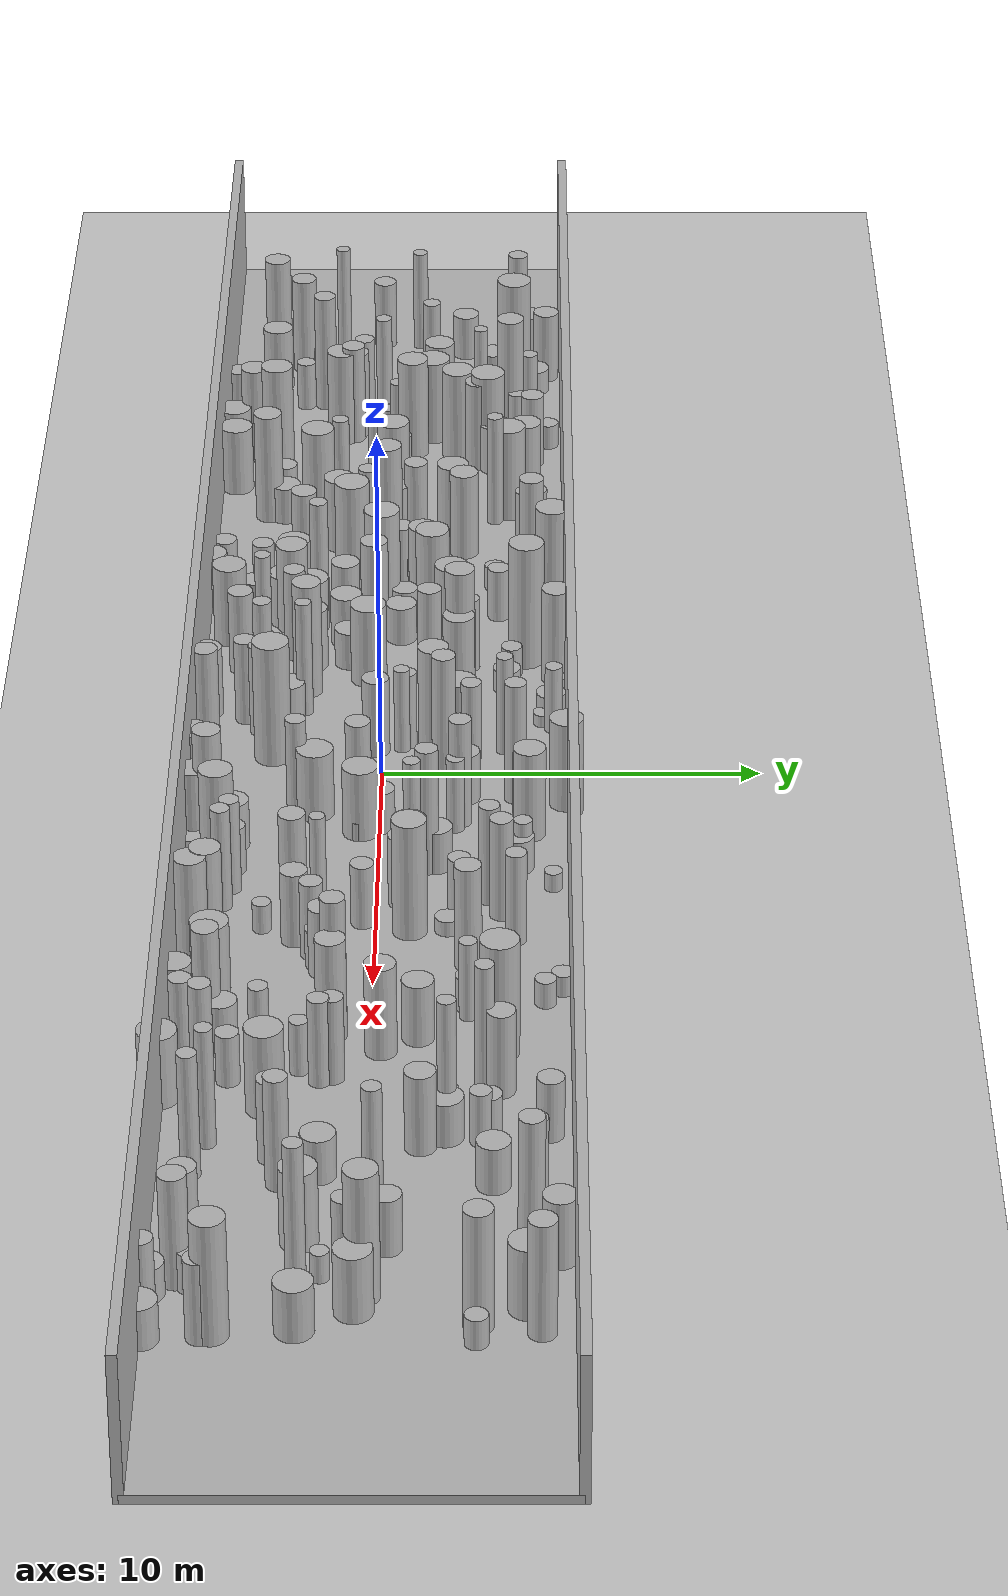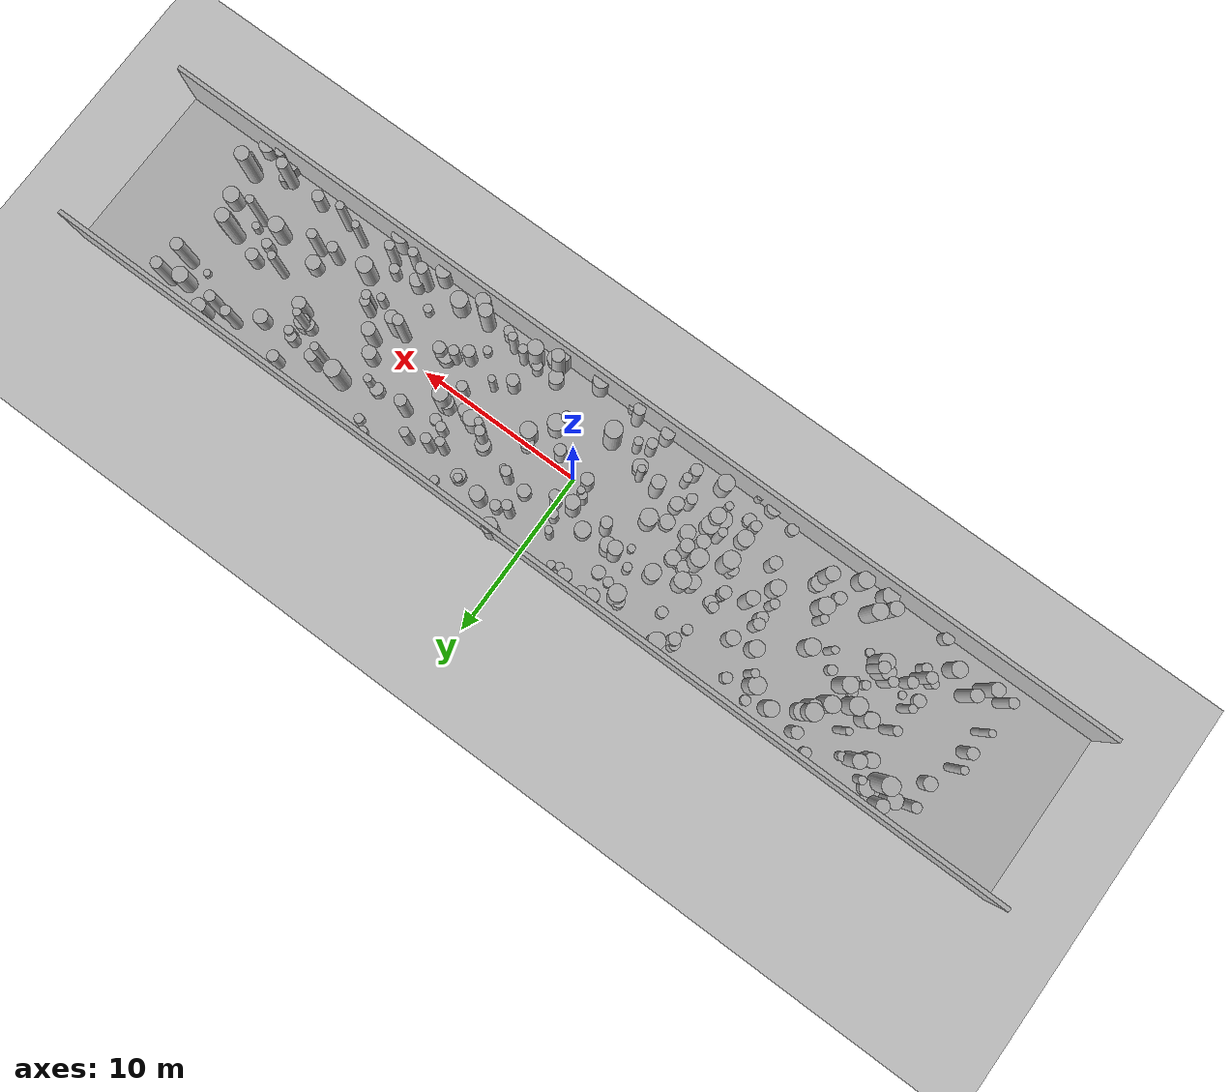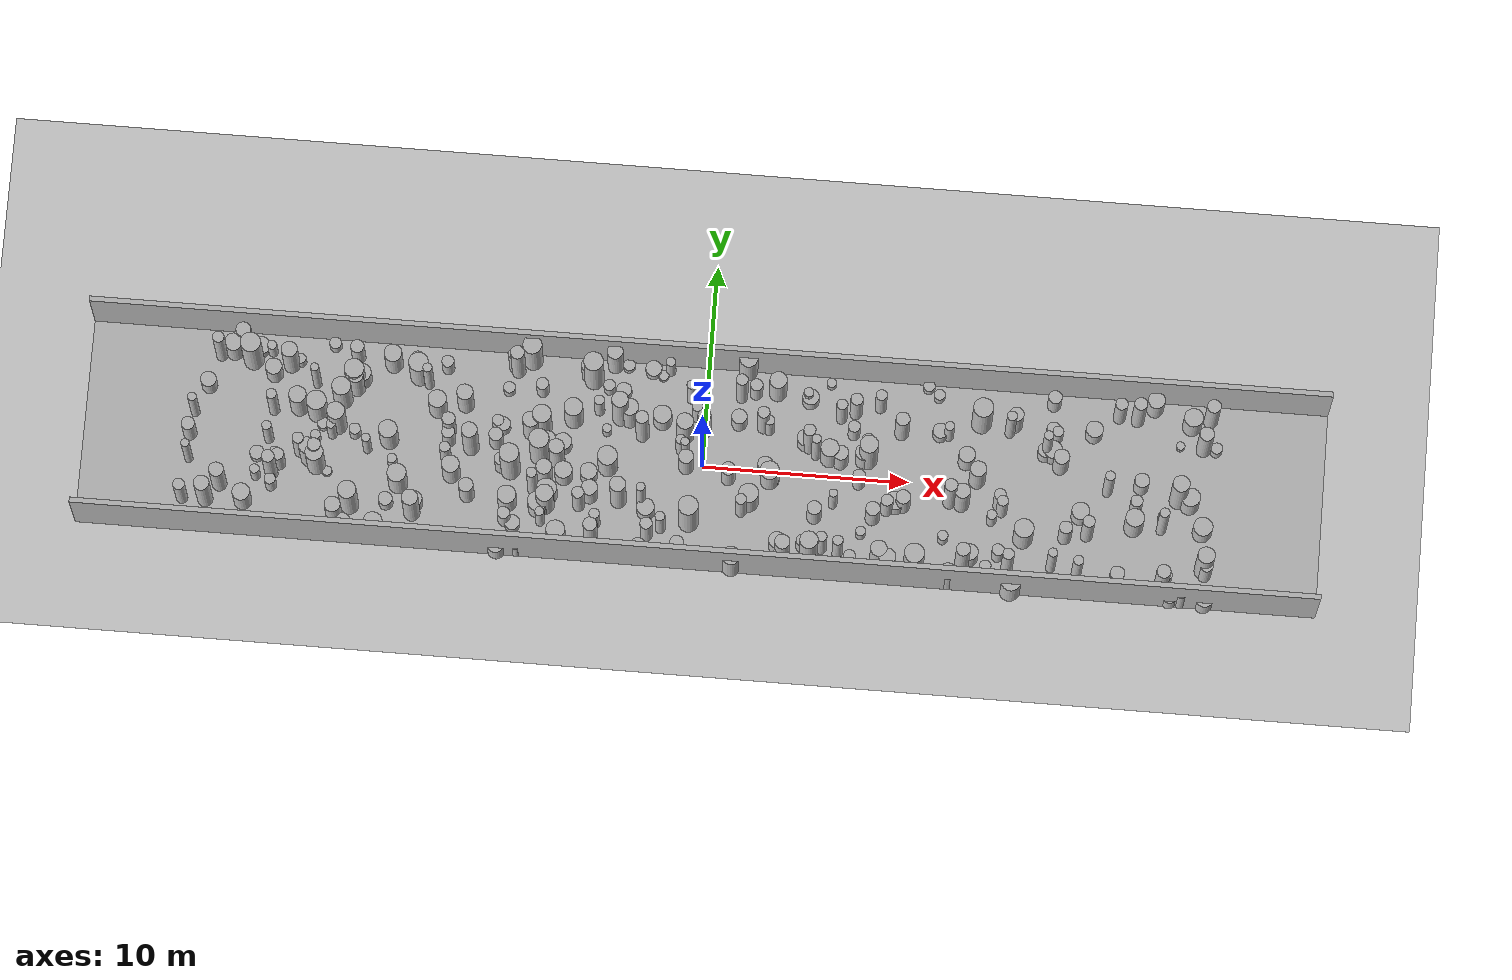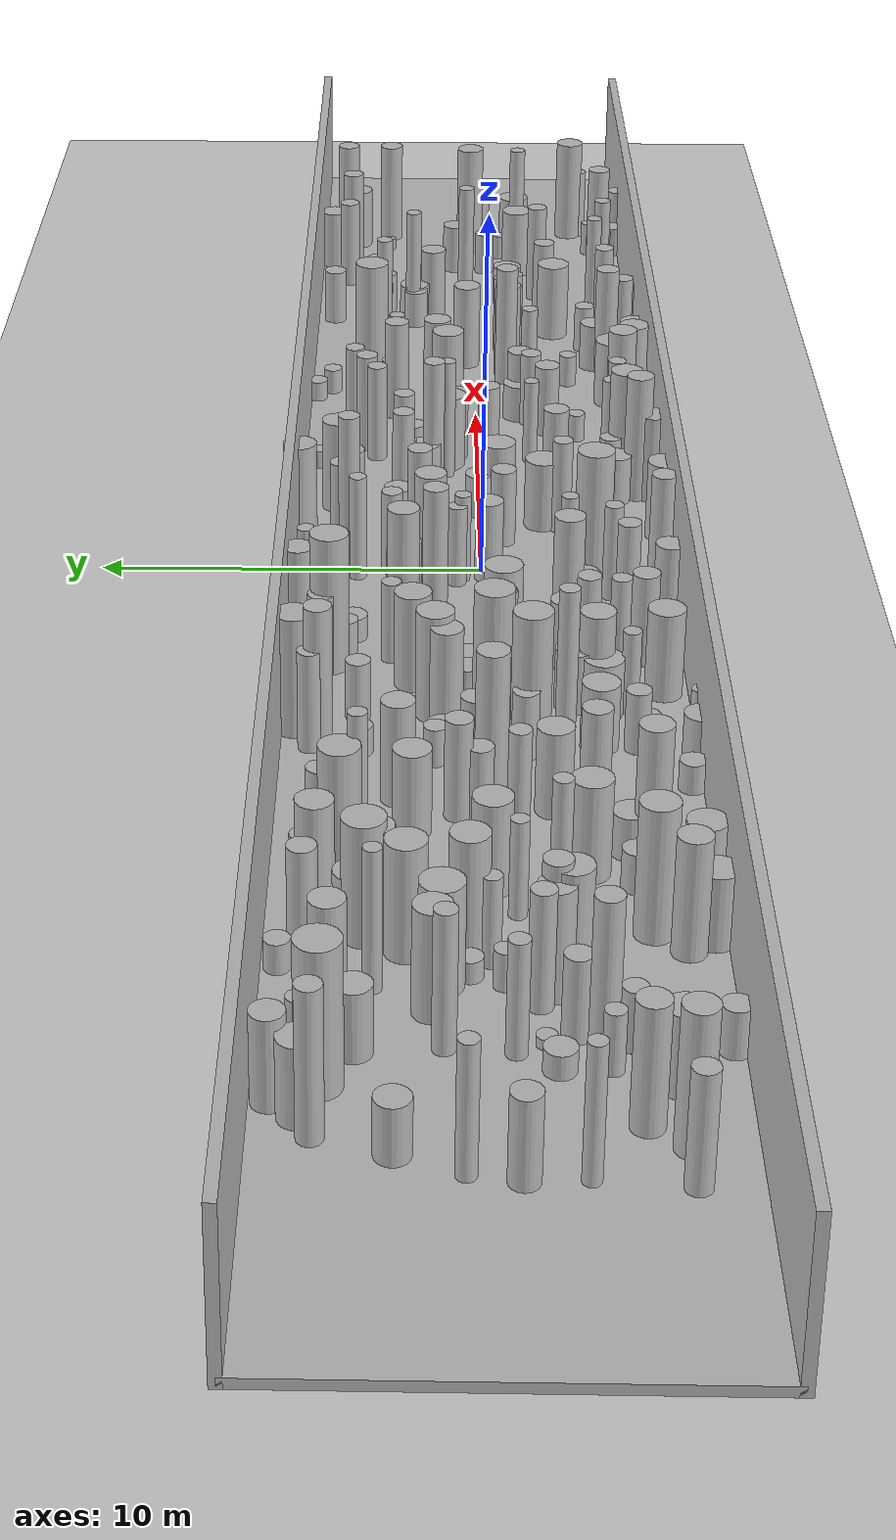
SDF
<?xml version="1.0"?>
<sdf version="1.4">
  <world name="default">
    <gui>
      <camera name="user_camera">
        <pose>-20 -30 40 0 0.66 0.83</pose>
      </camera>
    </gui>
    <include>
      <uri>model://ground_plane</uri>
    </include>
    <include>
      <uri>model://sun</uri>
    </include>
    <scene>
      <shadows>0</shadows>
    </scene>
    <model name="forest">
      <static>true</static>
      <link name="cylinder0">
        <pose>-12.389913493122123 -0.6164857760160567 1.2789422149600733 0 0 0 </pose>
        <visual name="visual">
          <geometry>
            <cylinder>
              <radius>0.2640215659879026</radius>
              <length>2.5578844299201466</length>
            </cylinder>
          </geometry>
        </visual>
        <collision name="collision">
          <geometry>
            <cylinder>
              <radius>0.2640215659879026</radius>
              <length>2.5578844299201466</length>
            </cylinder>
          </geometry>
          <max_contacts>0</max_contacts>
        </collision>
      </link>
      <link name="cylinder1">
        <pose>-8.918453066813743 -3.6858028048861415 0.4585606323043887 0 0 0 </pose>
        <visual name="visual">
          <geometry>
            <cylinder>
              <radius>0.37176183712964606</radius>
              <length>0.9171212646087774</length>
            </cylinder>
          </geometry>
        </visual>
        <collision name="collision">
          <geometry>
            <cylinder>
              <radius>0.37176183712964606</radius>
              <length>0.9171212646087774</length>
            </cylinder>
          </geometry>
          <max_contacts>0</max_contacts>
        </collision>
      </link>
      <link name="cylinder2">
        <pose>-18.978339106760433 -1.155977682333047 1.4584447334064259 0 0 0 </pose>
        <visual name="visual">
          <geometry>
            <cylinder>
              <radius>0.41375714241988626</radius>
              <length>2.9168894668128518</length>
            </cylinder>
          </geometry>
        </visual>
        <collision name="collision">
          <geometry>
            <cylinder>
              <radius>0.41375714241988626</radius>
              <length>2.9168894668128518</length>
            </cylinder>
          </geometry>
          <max_contacts>0</max_contacts>
        </collision>
      </link>
      <link name="cylinder3">
        <pose>22.47887445626342 -4.178614569205978 1.642320482933423 0 0 0 </pose>
        <visual name="visual">
          <geometry>
            <cylinder>
              <radius>0.33752390658815884</radius>
              <length>3.284640965866846</length>
            </cylinder>
          </geometry>
        </visual>
        <collision name="collision">
          <geometry>
            <cylinder>
              <radius>0.33752390658815884</radius>
              <length>3.284640965866846</length>
            </cylinder>
          </geometry>
          <max_contacts>0</max_contacts>
        </collision>
      </link>
      <link name="cylinder4">
        <pose>14.5302731458887 -3.3634032457613463 0.8396608742634206 0 0 0 </pose>
        <visual name="visual">
          <geometry>
            <cylinder>
              <radius>0.2939214647751605</radius>
              <length>1.6793217485268412</length>
            </cylinder>
          </geometry>
        </visual>
        <collision name="collision">
          <geometry>
            <cylinder>
              <radius>0.2939214647751605</radius>
              <length>1.6793217485268412</length>
            </cylinder>
          </geometry>
          <max_contacts>0</max_contacts>
        </collision>
      </link>
      <link name="cylinder5">
        <pose>18.362684909089495 -4.056848362321382 1.8538777930647994 0 0 0 </pose>
        <visual name="visual">
          <geometry>
            <cylinder>
              <radius>0.24213329332748434</radius>
              <length>3.7077555861295988</length>
            </cylinder>
          </geometry>
        </visual>
        <collision name="collision">
          <geometry>
            <cylinder>
              <radius>0.24213329332748434</radius>
              <length>3.7077555861295988</length>
            </cylinder>
          </geometry>
          <max_contacts>0</max_contacts>
        </collision>
      </link>
      <link name="cylinder6">
        <pose>3.5185023814617473 -0.5289069852324024 0.39152121170595017 0 0 0 </pose>
        <visual name="visual">
          <geometry>
            <cylinder>
              <radius>0.23570214300902984</radius>
              <length>0.7830424234119003</length>
            </cylinder>
          </geometry>
        </visual>
        <collision name="collision">
          <geometry>
            <cylinder>
              <radius>0.23570214300902984</radius>
              <length>0.7830424234119003</length>
            </cylinder>
          </geometry>
          <max_contacts>0</max_contacts>
        </collision>
      </link>
      <link name="cylinder7">
        <pose>-16.761811264655652 2.964869043372569 0.8588262211649531 0 0 0 </pose>
        <visual name="visual">
          <geometry>
            <cylinder>
              <radius>0.46347730381025604</radius>
              <length>1.7176524423299062</length>
            </cylinder>
          </geometry>
        </visual>
        <collision name="collision">
          <geometry>
            <cylinder>
              <radius>0.46347730381025604</radius>
              <length>1.7176524423299062</length>
            </cylinder>
          </geometry>
          <max_contacts>0</max_contacts>
        </collision>
      </link>
      <link name="cylinder8">
        <pose>-9.667703603242755 -0.8389615528529255 0.9886777490439089 0 0 0 </pose>
        <visual name="visual">
          <geometry>
            <cylinder>
              <radius>0.3212503952877882</radius>
              <length>1.9773554980878179</length>
            </cylinder>
          </geometry>
        </visual>
        <collision name="collision">
          <geometry>
            <cylinder>
              <radius>0.3212503952877882</radius>
              <length>1.9773554980878179</length>
            </cylinder>
          </geometry>
          <max_contacts>0</max_contacts>
        </collision>
      </link>
      <link name="cylinder9">
        <pose>-23.665607546349648 3.6394062842845454 1.9011852466170696 0 0 0 </pose>
        <visual name="visual">
          <geometry>
            <cylinder>
              <radius>0.28236321037003426</radius>
              <length>3.802370493234139</length>
            </cylinder>
          </geometry>
        </visual>
        <collision name="collision">
          <geometry>
            <cylinder>
              <radius>0.28236321037003426</radius>
              <length>3.802370493234139</length>
            </cylinder>
          </geometry>
          <max_contacts>0</max_contacts>
        </collision>
      </link>
      <link name="cylinder10">
        <pose>-21.005215314367547 -0.3415815577288628 1.4994202685417108 0 0 0 </pose>
        <visual name="visual">
          <geometry>
            <cylinder>
              <radius>0.23004852379547625</radius>
              <length>2.9988405370834217</length>
            </cylinder>
          </geometry>
        </visual>
        <collision name="collision">
          <geometry>
            <cylinder>
              <radius>0.23004852379547625</radius>
              <length>2.9988405370834217</length>
            </cylinder>
          </geometry>
          <max_contacts>0</max_contacts>
        </collision>
      </link>
      <link name="cylinder11">
        <pose>3.3686679684352363 3.89141718580448 1.4260544371908483 0 0 0 </pose>
        <visual name="visual">
          <geometry>
            <cylinder>
              <radius>0.4224523152110262</radius>
              <length>2.8521088743816967</length>
            </cylinder>
          </geometry>
        </visual>
        <collision name="collision">
          <geometry>
            <cylinder>
              <radius>0.4224523152110262</radius>
              <length>2.8521088743816967</length>
            </cylinder>
          </geometry>
          <max_contacts>0</max_contacts>
        </collision>
      </link>
      <link name="cylinder12">
        <pose>-17.061415783212418 -4.5929543059022855 1.036291618223426 0 0 0 </pose>
        <visual name="visual">
          <geometry>
            <cylinder>
              <radius>0.4613177867696143</radius>
              <length>2.072583236446852</length>
            </cylinder>
          </geometry>
        </visual>
        <collision name="collision">
          <geometry>
            <cylinder>
              <radius>0.4613177867696143</radius>
              <length>2.072583236446852</length>
            </cylinder>
          </geometry>
          <max_contacts>0</max_contacts>
        </collision>
      </link>
      <link name="cylinder13">
        <pose>6.527799041859339 2.8709751118988 1.543872692518495 0 0 0 </pose>
        <visual name="visual">
          <geometry>
            <cylinder>
              <radius>0.2687122442359387</radius>
              <length>3.08774538503699</length>
            </cylinder>
          </geometry>
        </visual>
        <collision name="collision">
          <geometry>
            <cylinder>
              <radius>0.2687122442359387</radius>
              <length>3.08774538503699</length>
            </cylinder>
          </geometry>
          <max_contacts>0</max_contacts>
        </collision>
      </link>
      <link name="cylinder14">
        <pose>5.428768677006516 0.9108389063789977 1.8576229997360225 0 0 0 </pose>
        <visual name="visual">
          <geometry>
            <cylinder>
              <radius>0.22108412347359485</radius>
              <length>3.715245999472045</length>
            </cylinder>
          </geometry>
        </visual>
        <collision name="collision">
          <geometry>
            <cylinder>
              <radius>0.22108412347359485</radius>
              <length>3.715245999472045</length>
            </cylinder>
          </geometry>
          <max_contacts>0</max_contacts>
        </collision>
      </link>
      <link name="cylinder15">
        <pose>-21.503227747067015 -1.1797395255265641 0.41484440350514384 0 0 0 </pose>
        <visual name="visual">
          <geometry>
            <cylinder>
              <radius>0.35250127038315193</radius>
              <length>0.8296888070102877</length>
            </cylinder>
          </geometry>
        </visual>
        <collision name="collision">
          <geometry>
            <cylinder>
              <radius>0.35250127038315193</radius>
              <length>0.8296888070102877</length>
            </cylinder>
          </geometry>
          <max_contacts>0</max_contacts>
        </collision>
      </link>
      <link name="cylinder16">
        <pose>10.526784670415744 -3.9707757080040986 1.1181079721017348 0 0 0 </pose>
        <visual name="visual">
          <geometry>
            <cylinder>
              <radius>0.48806112289139036</radius>
              <length>2.2362159442034697</length>
            </cylinder>
          </geometry>
        </visual>
        <collision name="collision">
          <geometry>
            <cylinder>
              <radius>0.48806112289139036</radius>
              <length>2.2362159442034697</length>
            </cylinder>
          </geometry>
          <max_contacts>0</max_contacts>
        </collision>
      </link>
      <link name="cylinder17">
        <pose>1.8629100106519232 4.8554674358730505 1.424527879419971 0 0 0 </pose>
        <visual name="visual">
          <geometry>
            <cylinder>
              <radius>0.44336391330813085</radius>
              <length>2.849055758839942</length>
            </cylinder>
          </geometry>
        </visual>
        <collision name="collision">
          <geometry>
            <cylinder>
              <radius>0.44336391330813085</radius>
              <length>2.849055758839942</length>
            </cylinder>
          </geometry>
          <max_contacts>0</max_contacts>
        </collision>
      </link>
      <link name="cylinder18">
        <pose>7.4240206471141335 -4.251918299851472 0.9027344437147206 0 0 0 </pose>
        <visual name="visual">
          <geometry>
            <cylinder>
              <radius>0.2934277185561901</radius>
              <length>1.8054688874294411</length>
            </cylinder>
          </geometry>
        </visual>
        <collision name="collision">
          <geometry>
            <cylinder>
              <radius>0.2934277185561901</radius>
              <length>1.8054688874294411</length>
            </cylinder>
          </geometry>
          <max_contacts>0</max_contacts>
        </collision>
      </link>
      <link name="cylinder19">
        <pose>16.74972533325966 4.350820737682305 0.9596957862691741 0 0 0 </pose>
        <visual name="visual">
          <geometry>
            <cylinder>
              <radius>0.330943244393582</radius>
              <length>1.9193915725383481</length>
            </cylinder>
          </geometry>
        </visual>
        <collision name="collision">
          <geometry>
            <cylinder>
              <radius>0.330943244393582</radius>
              <length>1.9193915725383481</length>
            </cylinder>
          </geometry>
          <max_contacts>0</max_contacts>
        </collision>
      </link>
      <link name="cylinder20">
        <pose>-4.582425894276419 4.630502443168245 1.5284561691394896 0 0 0 </pose>
        <visual name="visual">
          <geometry>
            <cylinder>
              <radius>0.38533006311853774</radius>
              <length>3.056912338278979</length>
            </cylinder>
          </geometry>
        </visual>
        <collision name="collision">
          <geometry>
            <cylinder>
              <radius>0.38533006311853774</radius>
              <length>3.056912338278979</length>
            </cylinder>
          </geometry>
          <max_contacts>0</max_contacts>
        </collision>
      </link>
      <link name="cylinder21">
        <pose>13.937974852405098 -4.483488352646551 1.4200845603587593 0 0 0 </pose>
        <visual name="visual">
          <geometry>
            <cylinder>
              <radius>0.2839657664903985</radius>
              <length>2.8401691207175186</length>
            </cylinder>
          </geometry>
        </visual>
        <collision name="collision">
          <geometry>
            <cylinder>
              <radius>0.2839657664903985</radius>
              <length>2.8401691207175186</length>
            </cylinder>
          </geometry>
          <max_contacts>0</max_contacts>
        </collision>
      </link>
      <link name="cylinder22">
        <pose>-2.8038115602074143 -2.1017270554419665 1.8182717871537928 0 0 0 </pose>
        <visual name="visual">
          <geometry>
            <cylinder>
              <radius>0.21597443946958594</radius>
              <length>3.6365435743075856</length>
            </cylinder>
          </geometry>
        </visual>
        <collision name="collision">
          <geometry>
            <cylinder>
              <radius>0.21597443946958594</radius>
              <length>3.6365435743075856</length>
            </cylinder>
          </geometry>
          <max_contacts>0</max_contacts>
        </collision>
      </link>
      <link name="cylinder23">
        <pose>23.591305482721907 -0.12271582391579372 1.0166009628938495 0 0 0 </pose>
        <visual name="visual">
          <geometry>
            <cylinder>
              <radius>0.46206444477825864</radius>
              <length>2.033201925787699</length>
            </cylinder>
          </geometry>
        </visual>
        <collision name="collision">
          <geometry>
            <cylinder>
              <radius>0.46206444477825864</radius>
              <length>2.033201925787699</length>
            </cylinder>
          </geometry>
          <max_contacts>0</max_contacts>
        </collision>
      </link>
      <link name="cylinder24">
        <pose>5.068609548155727 1.282792792949734 1.9314872287129736 0 0 0 </pose>
        <visual name="visual">
          <geometry>
            <cylinder>
              <radius>0.2920961110066845</radius>
              <length>3.8629744574259473</length>
            </cylinder>
          </geometry>
        </visual>
        <collision name="collision">
          <geometry>
            <cylinder>
              <radius>0.2920961110066845</radius>
              <length>3.8629744574259473</length>
            </cylinder>
          </geometry>
          <max_contacts>0</max_contacts>
        </collision>
      </link>
      <link name="cylinder25">
        <pose>-21.779436015058096 4.115555588904252 0.491929286126674 0 0 0 </pose>
        <visual name="visual">
          <geometry>
            <cylinder>
              <radius>0.4418668476225953</radius>
              <length>0.983858572253348</length>
            </cylinder>
          </geometry>
        </visual>
        <collision name="collision">
          <geometry>
            <cylinder>
              <radius>0.4418668476225953</radius>
              <length>0.983858572253348</length>
            </cylinder>
          </geometry>
          <max_contacts>0</max_contacts>
        </collision>
      </link>
      <link name="cylinder26">
        <pose>-18.742497188077866 -0.1580609581002843 0.5917921316678002 0 0 0 </pose>
        <visual name="visual">
          <geometry>
            <cylinder>
              <radius>0.2432426239660913</radius>
              <length>1.1835842633356004</length>
            </cylinder>
          </geometry>
        </visual>
        <collision name="collision">
          <geometry>
            <cylinder>
              <radius>0.2432426239660913</radius>
              <length>1.1835842633356004</length>
            </cylinder>
          </geometry>
          <max_contacts>0</max_contacts>
        </collision>
      </link>
      <link name="cylinder27">
        <pose>-4.551818297995101 -0.4273532509292117 1.2950522131416735 0 0 0 </pose>
        <visual name="visual">
          <geometry>
            <cylinder>
              <radius>0.4851396762435782</radius>
              <length>2.590104426283347</length>
            </cylinder>
          </geometry>
        </visual>
        <collision name="collision">
          <geometry>
            <cylinder>
              <radius>0.4851396762435782</radius>
              <length>2.590104426283347</length>
            </cylinder>
          </geometry>
          <max_contacts>0</max_contacts>
        </collision>
      </link>
      <link name="cylinder28">
        <pose>9.447276060925681 -1.22654271336321 0.6619986889347537 0 0 0 </pose>
        <visual name="visual">
          <geometry>
            <cylinder>
              <radius>0.4639562166751768</radius>
              <length>1.3239973778695073</length>
            </cylinder>
          </geometry>
        </visual>
        <collision name="collision">
          <geometry>
            <cylinder>
              <radius>0.4639562166751768</radius>
              <length>1.3239973778695073</length>
            </cylinder>
          </geometry>
          <max_contacts>0</max_contacts>
        </collision>
      </link>
      <link name="cylinder29">
        <pose>-0.03519675320470128 1.655959014261005 1.8078357501995028 0 0 0 </pose>
        <visual name="visual">
          <geometry>
            <cylinder>
              <radius>0.3177926499357096</radius>
              <length>3.6156715003990056</length>
            </cylinder>
          </geometry>
        </visual>
        <collision name="collision">
          <geometry>
            <cylinder>
              <radius>0.3177926499357096</radius>
              <length>3.6156715003990056</length>
            </cylinder>
          </geometry>
          <max_contacts>0</max_contacts>
        </collision>
      </link>
      <link name="cylinder30">
        <pose>-9.5906438474116 -4.92725049409366 0.6952648383239067 0 0 0 </pose>
        <visual name="visual">
          <geometry>
            <cylinder>
              <radius>0.4296117749040066</radius>
              <length>1.3905296766478135</length>
            </cylinder>
          </geometry>
        </visual>
        <collision name="collision">
          <geometry>
            <cylinder>
              <radius>0.4296117749040066</radius>
              <length>1.3905296766478135</length>
            </cylinder>
          </geometry>
          <max_contacts>0</max_contacts>
        </collision>
      </link>
      <link name="cylinder31">
        <pose>9.23183586181289 -4.492843921649491 1.6333624161777784 0 0 0 </pose>
        <visual name="visual">
          <geometry>
            <cylinder>
              <radius>0.4136812708600509</radius>
              <length>3.266724832355557</length>
            </cylinder>
          </geometry>
        </visual>
        <collision name="collision">
          <geometry>
            <cylinder>
              <radius>0.4136812708600509</radius>
              <length>3.266724832355557</length>
            </cylinder>
          </geometry>
          <max_contacts>0</max_contacts>
        </collision>
      </link>
      <link name="cylinder32">
        <pose>17.690212783013152 -2.2081494208562455 1.2673248724445154 0 0 0 </pose>
        <visual name="visual">
          <geometry>
            <cylinder>
              <radius>0.3199982120551544</radius>
              <length>2.534649744889031</length>
            </cylinder>
          </geometry>
        </visual>
        <collision name="collision">
          <geometry>
            <cylinder>
              <radius>0.3199982120551544</radius>
              <length>2.534649744889031</length>
            </cylinder>
          </geometry>
          <max_contacts>0</max_contacts>
        </collision>
      </link>
      <link name="cylinder33">
        <pose>4.9791727919138715 3.6066872790392157 0.6087659169997937 0 0 0 </pose>
        <visual name="visual">
          <geometry>
            <cylinder>
              <radius>0.40601135492092966</radius>
              <length>1.2175318339995873</length>
            </cylinder>
          </geometry>
        </visual>
        <collision name="collision">
          <geometry>
            <cylinder>
              <radius>0.40601135492092966</radius>
              <length>1.2175318339995873</length>
            </cylinder>
          </geometry>
          <max_contacts>0</max_contacts>
        </collision>
      </link>
      <link name="cylinder34">
        <pose>-20.23513384234424 3.4125626318916957 1.6848206293768455 0 0 0 </pose>
        <visual name="visual">
          <geometry>
            <cylinder>
              <radius>0.3905785535304223</radius>
              <length>3.369641258753691</length>
            </cylinder>
          </geometry>
        </visual>
        <collision name="collision">
          <geometry>
            <cylinder>
              <radius>0.3905785535304223</radius>
              <length>3.369641258753691</length>
            </cylinder>
          </geometry>
          <max_contacts>0</max_contacts>
        </collision>
      </link>
      <link name="cylinder35">
        <pose>-8.36797537119746 0.9935382336451521 1.450762492947488 0 0 0 </pose>
        <visual name="visual">
          <geometry>
            <cylinder>
              <radius>0.39625561410346916</radius>
              <length>2.901524985894976</length>
            </cylinder>
          </geometry>
        </visual>
        <collision name="collision">
          <geometry>
            <cylinder>
              <radius>0.39625561410346916</radius>
              <length>2.901524985894976</length>
            </cylinder>
          </geometry>
          <max_contacts>0</max_contacts>
        </collision>
      </link>
      <link name="cylinder36">
        <pose>-9.331027541366948 -3.4661809195663063 0.9193993759060639 0 0 0 </pose>
        <visual name="visual">
          <geometry>
            <cylinder>
              <radius>0.3020906780574557</radius>
              <length>1.8387987518121278</length>
            </cylinder>
          </geometry>
        </visual>
        <collision name="collision">
          <geometry>
            <cylinder>
              <radius>0.3020906780574557</radius>
              <length>1.8387987518121278</length>
            </cylinder>
          </geometry>
          <max_contacts>0</max_contacts>
        </collision>
      </link>
      <link name="cylinder37">
        <pose>-7.121782881938877 0.5288827580215489 0.6344651029781753 0 0 0 </pose>
        <visual name="visual">
          <geometry>
            <cylinder>
              <radius>0.20164770665736817</radius>
              <length>1.2689302059563505</length>
            </cylinder>
          </geometry>
        </visual>
        <collision name="collision">
          <geometry>
            <cylinder>
              <radius>0.20164770665736817</radius>
              <length>1.2689302059563505</length>
            </cylinder>
          </geometry>
          <max_contacts>0</max_contacts>
        </collision>
      </link>
      <link name="cylinder38">
        <pose>11.772968325162793 2.3713193202402127 1.2347113408801815 0 0 0 </pose>
        <visual name="visual">
          <geometry>
            <cylinder>
              <radius>0.22609128089160999</radius>
              <length>2.469422681760363</length>
            </cylinder>
          </geometry>
        </visual>
        <collision name="collision">
          <geometry>
            <cylinder>
              <radius>0.22609128089160999</radius>
              <length>2.469422681760363</length>
            </cylinder>
          </geometry>
          <max_contacts>0</max_contacts>
        </collision>
      </link>
      <link name="cylinder39">
        <pose>-6.638270380893967 -1.0880244645927197 0.8703303389355472 0 0 0 </pose>
        <visual name="visual">
          <geometry>
            <cylinder>
              <radius>0.4321729143397579</radius>
              <length>1.7406606778710945</length>
            </cylinder>
          </geometry>
        </visual>
        <collision name="collision">
          <geometry>
            <cylinder>
              <radius>0.4321729143397579</radius>
              <length>1.7406606778710945</length>
            </cylinder>
          </geometry>
          <max_contacts>0</max_contacts>
        </collision>
      </link>
      <link name="cylinder40">
        <pose>-18.599666781171827 -1.5019799856270377 1.5660669158370695 0 0 0 </pose>
        <visual name="visual">
          <geometry>
            <cylinder>
              <radius>0.44107084303791805</radius>
              <length>3.132133831674139</length>
            </cylinder>
          </geometry>
        </visual>
        <collision name="collision">
          <geometry>
            <cylinder>
              <radius>0.44107084303791805</radius>
              <length>3.132133831674139</length>
            </cylinder>
          </geometry>
          <max_contacts>0</max_contacts>
        </collision>
      </link>
      <link name="cylinder41">
        <pose>-2.7175389624674793 4.491068459604094 0.4643532162588451 0 0 0 </pose>
        <visual name="visual">
          <geometry>
            <cylinder>
              <radius>0.3949513655718183</radius>
              <length>0.9287064325176903</length>
            </cylinder>
          </geometry>
        </visual>
        <collision name="collision">
          <geometry>
            <cylinder>
              <radius>0.3949513655718183</radius>
              <length>0.9287064325176903</length>
            </cylinder>
          </geometry>
          <max_contacts>0</max_contacts>
        </collision>
      </link>
      <link name="cylinder42">
        <pose>5.435321524717381 -4.030631602253351 1.7378331856041922 0 0 0 </pose>
        <visual name="visual">
          <geometry>
            <cylinder>
              <radius>0.4397327907778434</radius>
              <length>3.4756663712083844</length>
            </cylinder>
          </geometry>
        </visual>
        <collision name="collision">
          <geometry>
            <cylinder>
              <radius>0.4397327907778434</radius>
              <length>3.4756663712083844</length>
            </cylinder>
          </geometry>
          <max_contacts>0</max_contacts>
        </collision>
      </link>
      <link name="cylinder43">
        <pose>-0.42939339879843885 2.3731249413525664 1.2807768209993284 0 0 0 </pose>
        <visual name="visual">
          <geometry>
            <cylinder>
              <radius>0.2696798974898803</radius>
              <length>2.561553641998657</length>
            </cylinder>
          </geometry>
        </visual>
        <collision name="collision">
          <geometry>
            <cylinder>
              <radius>0.2696798974898803</radius>
              <length>2.561553641998657</length>
            </cylinder>
          </geometry>
          <max_contacts>0</max_contacts>
        </collision>
      </link>
      <link name="cylinder44">
        <pose>-13.990156403138032 3.3505663086298014 1.5324832089418257 0 0 0 </pose>
        <visual name="visual">
          <geometry>
            <cylinder>
              <radius>0.4783362634145502</radius>
              <length>3.0649664178836513</length>
            </cylinder>
          </geometry>
        </visual>
        <collision name="collision">
          <geometry>
            <cylinder>
              <radius>0.4783362634145502</radius>
              <length>3.0649664178836513</length>
            </cylinder>
          </geometry>
          <max_contacts>0</max_contacts>
        </collision>
      </link>
      <link name="cylinder45">
        <pose>-9.241455031519507 3.98643197940304 1.9590375152031578 0 0 0 </pose>
        <visual name="visual">
          <geometry>
            <cylinder>
              <radius>0.3376911724527055</radius>
              <length>3.9180750304063157</length>
            </cylinder>
          </geometry>
        </visual>
        <collision name="collision">
          <geometry>
            <cylinder>
              <radius>0.3376911724527055</radius>
              <length>3.9180750304063157</length>
            </cylinder>
          </geometry>
          <max_contacts>0</max_contacts>
        </collision>
      </link>
      <link name="cylinder46">
        <pose>-7.584552236493696 -3.4042703069322378 1.2165378588113809 0 0 0 </pose>
        <visual name="visual">
          <geometry>
            <cylinder>
              <radius>0.22346558559214158</radius>
              <length>2.4330757176227618</length>
            </cylinder>
          </geometry>
        </visual>
        <collision name="collision">
          <geometry>
            <cylinder>
              <radius>0.22346558559214158</radius>
              <length>2.4330757176227618</length>
            </cylinder>
          </geometry>
          <max_contacts>0</max_contacts>
        </collision>
      </link>
      <link name="cylinder47">
        <pose>-23.813632729153195 -3.5745698049681685 1.7897251551725513 0 0 0 </pose>
        <visual name="visual">
          <geometry>
            <cylinder>
              <radius>0.37790018455302027</radius>
              <length>3.5794503103451025</length>
            </cylinder>
          </geometry>
        </visual>
        <collision name="collision">
          <geometry>
            <cylinder>
              <radius>0.37790018455302027</radius>
              <length>3.5794503103451025</length>
            </cylinder>
          </geometry>
          <max_contacts>0</max_contacts>
        </collision>
      </link>
      <link name="cylinder48">
        <pose>-18.751007569529488 1.1397680272205015 1.408767534734153 0 0 0 </pose>
        <visual name="visual">
          <geometry>
            <cylinder>
              <radius>0.4893086770583015</radius>
              <length>2.817535069468306</length>
            </cylinder>
          </geometry>
        </visual>
        <collision name="collision">
          <geometry>
            <cylinder>
              <radius>0.4893086770583015</radius>
              <length>2.817535069468306</length>
            </cylinder>
          </geometry>
          <max_contacts>0</max_contacts>
        </collision>
      </link>
      <link name="cylinder49">
        <pose>15.244924607517909 -4.980480041222028 1.1135552518364316 0 0 0 </pose>
        <visual name="visual">
          <geometry>
            <cylinder>
              <radius>0.4966979918305741</radius>
              <length>2.227110503672863</length>
            </cylinder>
          </geometry>
        </visual>
        <collision name="collision">
          <geometry>
            <cylinder>
              <radius>0.4966979918305741</radius>
              <length>2.227110503672863</length>
            </cylinder>
          </geometry>
          <max_contacts>0</max_contacts>
        </collision>
      </link>
      <link name="cylinder50">
        <pose>8.378996921225344 3.540174057202499 1.4279590609195483 0 0 0 </pose>
        <visual name="visual">
          <geometry>
            <cylinder>
              <radius>0.2707541495920716</radius>
              <length>2.8559181218390965</length>
            </cylinder>
          </geometry>
        </visual>
        <collision name="collision">
          <geometry>
            <cylinder>
              <radius>0.2707541495920716</radius>
              <length>2.8559181218390965</length>
            </cylinder>
          </geometry>
          <max_contacts>0</max_contacts>
        </collision>
      </link>
      <link name="cylinder51">
        <pose>-18.627392296456655 -1.1775298522866207 1.6448311978323424 0 0 0 </pose>
        <visual name="visual">
          <geometry>
            <cylinder>
              <radius>0.3240482186157975</radius>
              <length>3.289662395664685</length>
            </cylinder>
          </geometry>
        </visual>
        <collision name="collision">
          <geometry>
            <cylinder>
              <radius>0.3240482186157975</radius>
              <length>3.289662395664685</length>
            </cylinder>
          </geometry>
          <max_contacts>0</max_contacts>
        </collision>
      </link>
      <link name="cylinder52">
        <pose>-5.837591543482734 4.02184528055051 1.2111605436664326 0 0 0 </pose>
        <visual name="visual">
          <geometry>
            <cylinder>
              <radius>0.34190522518814903</radius>
              <length>2.422321087332865</length>
            </cylinder>
          </geometry>
        </visual>
        <collision name="collision">
          <geometry>
            <cylinder>
              <radius>0.34190522518814903</radius>
              <length>2.422321087332865</length>
            </cylinder>
          </geometry>
          <max_contacts>0</max_contacts>
        </collision>
      </link>
      <link name="cylinder53">
        <pose>-6.78520961096234 0.41298843062179547 0.6803893124168536 0 0 0 </pose>
        <visual name="visual">
          <geometry>
            <cylinder>
              <radius>0.42122331053432893</radius>
              <length>1.3607786248337073</length>
            </cylinder>
          </geometry>
        </visual>
        <collision name="collision">
          <geometry>
            <cylinder>
              <radius>0.42122331053432893</radius>
              <length>1.3607786248337073</length>
            </cylinder>
          </geometry>
          <max_contacts>0</max_contacts>
        </collision>
      </link>
      <link name="cylinder54">
        <pose>1.292009153334039 -0.5652169246899916 1.2028669819020215 0 0 0 </pose>
        <visual name="visual">
          <geometry>
            <cylinder>
              <radius>0.3346198052062162</radius>
              <length>2.405733963804043</length>
            </cylinder>
          </geometry>
        </visual>
        <collision name="collision">
          <geometry>
            <cylinder>
              <radius>0.3346198052062162</radius>
              <length>2.405733963804043</length>
            </cylinder>
          </geometry>
          <max_contacts>0</max_contacts>
        </collision>
      </link>
      <link name="cylinder55">
        <pose>-6.375352558614871 1.7987873984926273 1.395333566689384 0 0 0 </pose>
        <visual name="visual">
          <geometry>
            <cylinder>
              <radius>0.45533462670216324</radius>
              <length>2.790667133378768</length>
            </cylinder>
          </geometry>
        </visual>
        <collision name="collision">
          <geometry>
            <cylinder>
              <radius>0.45533462670216324</radius>
              <length>2.790667133378768</length>
            </cylinder>
          </geometry>
          <max_contacts>0</max_contacts>
        </collision>
      </link>
      <link name="cylinder56">
        <pose>24.721061893447498 2.644003939974768 0.5281805942326888 0 0 0 </pose>
        <visual name="visual">
          <geometry>
            <cylinder>
              <radius>0.27994021403396574</radius>
              <length>1.0563611884653776</length>
            </cylinder>
          </geometry>
        </visual>
        <collision name="collision">
          <geometry>
            <cylinder>
              <radius>0.27994021403396574</radius>
              <length>1.0563611884653776</length>
            </cylinder>
          </geometry>
          <max_contacts>0</max_contacts>
        </collision>
      </link>
      <link name="cylinder57">
        <pose>24.449768140828063 -3.287925950227529 1.765528564776506 0 0 0 </pose>
        <visual name="visual">
          <geometry>
            <cylinder>
              <radius>0.4193288217632054</radius>
              <length>3.531057129553012</length>
            </cylinder>
          </geometry>
        </visual>
        <collision name="collision">
          <geometry>
            <cylinder>
              <radius>0.4193288217632054</radius>
              <length>3.531057129553012</length>
            </cylinder>
          </geometry>
          <max_contacts>0</max_contacts>
        </collision>
      </link>
      <link name="cylinder58">
        <pose>2.031621605337836 -2.1486612537931915 1.459682591462192 0 0 0 </pose>
        <visual name="visual">
          <geometry>
            <cylinder>
              <radius>0.2688347873922573</radius>
              <length>2.919365182924384</length>
            </cylinder>
          </geometry>
        </visual>
        <collision name="collision">
          <geometry>
            <cylinder>
              <radius>0.2688347873922573</radius>
              <length>2.919365182924384</length>
            </cylinder>
          </geometry>
          <max_contacts>0</max_contacts>
        </collision>
      </link>
      <link name="cylinder59">
        <pose>-18.447583648574795 0.5410527574651125 0.3898114863726291 0 0 0 </pose>
        <visual name="visual">
          <geometry>
            <cylinder>
              <radius>0.2815132785927279</radius>
              <length>0.7796229727452582</length>
            </cylinder>
          </geometry>
        </visual>
        <collision name="collision">
          <geometry>
            <cylinder>
              <radius>0.2815132785927279</radius>
              <length>0.7796229727452582</length>
            </cylinder>
          </geometry>
          <max_contacts>0</max_contacts>
        </collision>
      </link>
      <link name="cylinder60">
        <pose>6.817045257781796 -3.8611030398118116 1.585568934438507 0 0 0 </pose>
        <visual name="visual">
          <geometry>
            <cylinder>
              <radius>0.24852022485572434</radius>
              <length>3.171137868877014</length>
            </cylinder>
          </geometry>
        </visual>
        <collision name="collision">
          <geometry>
            <cylinder>
              <radius>0.24852022485572434</radius>
              <length>3.171137868877014</length>
            </cylinder>
          </geometry>
          <max_contacts>0</max_contacts>
        </collision>
      </link>
      <link name="cylinder61">
        <pose>-3.9157811447119037 4.613219586309514 0.35501372298618217 0 0 0 </pose>
        <visual name="visual">
          <geometry>
            <cylinder>
              <radius>0.28874540128218346</radius>
              <length>0.7100274459723643</length>
            </cylinder>
          </geometry>
        </visual>
        <collision name="collision">
          <geometry>
            <cylinder>
              <radius>0.28874540128218346</radius>
              <length>0.7100274459723643</length>
            </cylinder>
          </geometry>
          <max_contacts>0</max_contacts>
        </collision>
      </link>
      <link name="cylinder62">
        <pose>-10.014591206246791 0.34362689399675084 1.0119945949591194 0 0 0 </pose>
        <visual name="visual">
          <geometry>
            <cylinder>
              <radius>0.34261399047036256</radius>
              <length>2.0239891899182387</length>
            </cylinder>
          </geometry>
        </visual>
        <collision name="collision">
          <geometry>
            <cylinder>
              <radius>0.34261399047036256</radius>
              <length>2.0239891899182387</length>
            </cylinder>
          </geometry>
          <max_contacts>0</max_contacts>
        </collision>
      </link>
      <link name="cylinder63">
        <pose>-17.050070490331038 2.754622565069349 1.6094043688284676 0 0 0 </pose>
        <visual name="visual">
          <geometry>
            <cylinder>
              <radius>0.4843710857543946</radius>
              <length>3.218808737656935</length>
            </cylinder>
          </geometry>
        </visual>
        <collision name="collision">
          <geometry>
            <cylinder>
              <radius>0.4843710857543946</radius>
              <length>3.218808737656935</length>
            </cylinder>
          </geometry>
          <max_contacts>0</max_contacts>
        </collision>
      </link>
      <link name="cylinder64">
        <pose>-18.91274499381118 2.5448361576163467 1.8453397021543532 0 0 0 </pose>
        <visual name="visual">
          <geometry>
            <cylinder>
              <radius>0.202912345821084</radius>
              <length>3.6906794043087063</length>
            </cylinder>
          </geometry>
        </visual>
        <collision name="collision">
          <geometry>
            <cylinder>
              <radius>0.202912345821084</radius>
              <length>3.6906794043087063</length>
            </cylinder>
          </geometry>
          <max_contacts>0</max_contacts>
        </collision>
      </link>
      <link name="cylinder65">
        <pose>7.1845712540753865 2.1157544129979486 0.980823992264615 0 0 0 </pose>
        <visual name="visual">
          <geometry>
            <cylinder>
              <radius>0.2899675098013318</radius>
              <length>1.96164798452923</length>
            </cylinder>
          </geometry>
        </visual>
        <collision name="collision">
          <geometry>
            <cylinder>
              <radius>0.2899675098013318</radius>
              <length>1.96164798452923</length>
            </cylinder>
          </geometry>
          <max_contacts>0</max_contacts>
        </collision>
      </link>
      <link name="cylinder66">
        <pose>-9.741574770871807 1.1029626674739523 0.5774175398298544 0 0 0 </pose>
        <visual name="visual">
          <geometry>
            <cylinder>
              <radius>0.34965548821532144</radius>
              <length>1.1548350796597089</length>
            </cylinder>
          </geometry>
        </visual>
        <collision name="collision">
          <geometry>
            <cylinder>
              <radius>0.34965548821532144</radius>
              <length>1.1548350796597089</length>
            </cylinder>
          </geometry>
          <max_contacts>0</max_contacts>
        </collision>
      </link>
      <link name="cylinder67">
        <pose>-4.726940750155467 1.2831766855861932 0.5821106491188945 0 0 0 </pose>
        <visual name="visual">
          <geometry>
            <cylinder>
              <radius>0.21715590679515623</radius>
              <length>1.164221298237789</length>
            </cylinder>
          </geometry>
        </visual>
        <collision name="collision">
          <geometry>
            <cylinder>
              <radius>0.21715590679515623</radius>
              <length>1.164221298237789</length>
            </cylinder>
          </geometry>
          <max_contacts>0</max_contacts>
        </collision>
      </link>
      <link name="cylinder68">
        <pose>-8.06831903170766 -1.8586471831165174 1.9072403379446587 0 0 0 </pose>
        <visual name="visual">
          <geometry>
            <cylinder>
              <radius>0.2509423791881883</radius>
              <length>3.8144806758893175</length>
            </cylinder>
          </geometry>
        </visual>
        <collision name="collision">
          <geometry>
            <cylinder>
              <radius>0.2509423791881883</radius>
              <length>3.8144806758893175</length>
            </cylinder>
          </geometry>
          <max_contacts>0</max_contacts>
        </collision>
      </link>
      <link name="cylinder69">
        <pose>6.425788574674364 -1.4514245802739767 1.351874875211875 0 0 0 </pose>
        <visual name="visual">
          <geometry>
            <cylinder>
              <radius>0.20414401549664019</radius>
              <length>2.70374975042375</length>
            </cylinder>
          </geometry>
        </visual>
        <collision name="collision">
          <geometry>
            <cylinder>
              <radius>0.20414401549664019</radius>
              <length>2.70374975042375</length>
            </cylinder>
          </geometry>
          <max_contacts>0</max_contacts>
        </collision>
      </link>
      <link name="cylinder70">
        <pose>14.10962209428424 -1.669597794237422 0.8710236489371816 0 0 0 </pose>
        <visual name="visual">
          <geometry>
            <cylinder>
              <radius>0.24028268609505826</radius>
              <length>1.7420472978743633</length>
            </cylinder>
          </geometry>
        </visual>
        <collision name="collision">
          <geometry>
            <cylinder>
              <radius>0.24028268609505826</radius>
              <length>1.7420472978743633</length>
            </cylinder>
          </geometry>
          <max_contacts>0</max_contacts>
        </collision>
      </link>
      <link name="cylinder71">
        <pose>12.836077382744229 -3.9213283168496362 1.7799488736250846 0 0 0 </pose>
        <visual name="visual">
          <geometry>
            <cylinder>
              <radius>0.3387179983455981</radius>
              <length>3.559897747250169</length>
            </cylinder>
          </geometry>
        </visual>
        <collision name="collision">
          <geometry>
            <cylinder>
              <radius>0.3387179983455981</radius>
              <length>3.559897747250169</length>
            </cylinder>
          </geometry>
          <max_contacts>0</max_contacts>
        </collision>
      </link>
      <link name="cylinder72">
        <pose>-18.06195932043643 -1.763841210127942 0.2832955071213952 0 0 0 </pose>
        <visual name="visual">
          <geometry>
            <cylinder>
              <radius>0.23667020677883968</radius>
              <length>0.5665910142427903</length>
            </cylinder>
          </geometry>
        </visual>
        <collision name="collision">
          <geometry>
            <cylinder>
              <radius>0.23667020677883968</radius>
              <length>0.5665910142427903</length>
            </cylinder>
          </geometry>
          <max_contacts>0</max_contacts>
        </collision>
      </link>
      <link name="cylinder73">
        <pose>-20.80408796542286 -4.6534139892818605 0.6997406246825335 0 0 0 </pose>
        <visual name="visual">
          <geometry>
            <cylinder>
              <radius>0.3352127121600865</radius>
              <length>1.399481249365067</length>
            </cylinder>
          </geometry>
        </visual>
        <collision name="collision">
          <geometry>
            <cylinder>
              <radius>0.3352127121600865</radius>
              <length>1.399481249365067</length>
            </cylinder>
          </geometry>
          <max_contacts>0</max_contacts>
        </collision>
      </link>
      <link name="cylinder74">
        <pose>-11.044432887734168 -4.625905560917079 0.5063726596747875 0 0 0 </pose>
        <visual name="visual">
          <geometry>
            <cylinder>
              <radius>0.3305488003278912</radius>
              <length>1.012745319349575</length>
            </cylinder>
          </geometry>
        </visual>
        <collision name="collision">
          <geometry>
            <cylinder>
              <radius>0.3305488003278912</radius>
              <length>1.012745319349575</length>
            </cylinder>
          </geometry>
          <max_contacts>0</max_contacts>
        </collision>
      </link>
      <link name="cylinder75">
        <pose>-7.86339897560223 -0.11784825348554229 1.8417994693246726 0 0 0 </pose>
        <visual name="visual">
          <geometry>
            <cylinder>
              <radius>0.48812707964760427</radius>
              <length>3.6835989386493453</length>
            </cylinder>
          </geometry>
        </visual>
        <collision name="collision">
          <geometry>
            <cylinder>
              <radius>0.48812707964760427</radius>
              <length>3.6835989386493453</length>
            </cylinder>
          </geometry>
          <max_contacts>0</max_contacts>
        </collision>
      </link>
      <link name="cylinder76">
        <pose>14.934039233461384 3.1806282967403963 1.2902992635008506 0 0 0 </pose>
        <visual name="visual">
          <geometry>
            <cylinder>
              <radius>0.35341982849496534</radius>
              <length>2.580598527001701</length>
            </cylinder>
          </geometry>
        </visual>
        <collision name="collision">
          <geometry>
            <cylinder>
              <radius>0.35341982849496534</radius>
              <length>2.580598527001701</length>
            </cylinder>
          </geometry>
          <max_contacts>0</max_contacts>
        </collision>
      </link>
      <link name="cylinder77">
        <pose>-7.9929294260253485 3.0834245214219056 0.9000446579199859 0 0 0 </pose>
        <visual name="visual">
          <geometry>
            <cylinder>
              <radius>0.30213135898434745</radius>
              <length>1.8000893158399718</length>
            </cylinder>
          </geometry>
        </visual>
        <collision name="collision">
          <geometry>
            <cylinder>
              <radius>0.30213135898434745</radius>
              <length>1.8000893158399718</length>
            </cylinder>
          </geometry>
          <max_contacts>0</max_contacts>
        </collision>
      </link>
      <link name="cylinder78">
        <pose>13.17408756718443 -3.5818733198657613 0.844874332020402 0 0 0 </pose>
        <visual name="visual">
          <geometry>
            <cylinder>
              <radius>0.40805120420738106</radius>
              <length>1.689748664040804</length>
            </cylinder>
          </geometry>
        </visual>
        <collision name="collision">
          <geometry>
            <cylinder>
              <radius>0.40805120420738106</radius>
              <length>1.689748664040804</length>
            </cylinder>
          </geometry>
          <max_contacts>0</max_contacts>
        </collision>
      </link>
      <link name="cylinder79">
        <pose>-11.219268246103598 -0.016604221676278286 1.954229122500143 0 0 0 </pose>
        <visual name="visual">
          <geometry>
            <cylinder>
              <radius>0.38682470265564367</radius>
              <length>3.908458245000286</length>
            </cylinder>
          </geometry>
        </visual>
        <collision name="collision">
          <geometry>
            <cylinder>
              <radius>0.38682470265564367</radius>
              <length>3.908458245000286</length>
            </cylinder>
          </geometry>
          <max_contacts>0</max_contacts>
        </collision>
      </link>
      <link name="cylinder80">
        <pose>-15.539824815004266 -4.48462235163303 1.1319483732159765 0 0 0 </pose>
        <visual name="visual">
          <geometry>
            <cylinder>
              <radius>0.4620812686708832</radius>
              <length>2.263896746431953</length>
            </cylinder>
          </geometry>
        </visual>
        <collision name="collision">
          <geometry>
            <cylinder>
              <radius>0.4620812686708832</radius>
              <length>2.263896746431953</length>
            </cylinder>
          </geometry>
          <max_contacts>0</max_contacts>
        </collision>
      </link>
      <link name="cylinder81">
        <pose>18.761883628997865 3.008375247907537 0.7686204943772541 0 0 0 </pose>
        <visual name="visual">
          <geometry>
            <cylinder>
              <radius>0.41461164967951025</radius>
              <length>1.5372409887545082</length>
            </cylinder>
          </geometry>
        </visual>
        <collision name="collision">
          <geometry>
            <cylinder>
              <radius>0.41461164967951025</radius>
              <length>1.5372409887545082</length>
            </cylinder>
          </geometry>
          <max_contacts>0</max_contacts>
        </collision>
      </link>
      <link name="cylinder82">
        <pose>-11.223384397252717 -2.387317778088386 1.2332614786788882 0 0 0 </pose>
        <visual name="visual">
          <geometry>
            <cylinder>
              <radius>0.3580137096092616</radius>
              <length>2.4665229573577765</length>
            </cylinder>
          </geometry>
        </visual>
        <collision name="collision">
          <geometry>
            <cylinder>
              <radius>0.3580137096092616</radius>
              <length>2.4665229573577765</length>
            </cylinder>
          </geometry>
          <max_contacts>0</max_contacts>
        </collision>
      </link>
      <link name="cylinder83">
        <pose>6.023353920046702 -3.6814882866755028 1.470136975742704 0 0 0 </pose>
        <visual name="visual">
          <geometry>
            <cylinder>
              <radius>0.2607214959013141</radius>
              <length>2.940273951485408</length>
            </cylinder>
          </geometry>
        </visual>
        <collision name="collision">
          <geometry>
            <cylinder>
              <radius>0.2607214959013141</radius>
              <length>2.940273951485408</length>
            </cylinder>
          </geometry>
          <max_contacts>0</max_contacts>
        </collision>
      </link>
      <link name="cylinder84">
        <pose>20.964975878639045 -1.436609062028845 1.1974116911122923 0 0 0 </pose>
        <visual name="visual">
          <geometry>
            <cylinder>
              <radius>0.45776882402253655</radius>
              <length>2.3948233822245846</length>
            </cylinder>
          </geometry>
        </visual>
        <collision name="collision">
          <geometry>
            <cylinder>
              <radius>0.45776882402253655</radius>
              <length>2.3948233822245846</length>
            </cylinder>
          </geometry>
          <max_contacts>0</max_contacts>
        </collision>
      </link>
      <link name="cylinder85">
        <pose>-4.9479325844891555 -3.3142753631086483 1.232136252204616 0 0 0 </pose>
        <visual name="visual">
          <geometry>
            <cylinder>
              <radius>0.2583030177528004</radius>
              <length>2.464272504409232</length>
            </cylinder>
          </geometry>
        </visual>
        <collision name="collision">
          <geometry>
            <cylinder>
              <radius>0.2583030177528004</radius>
              <length>2.464272504409232</length>
            </cylinder>
          </geometry>
          <max_contacts>0</max_contacts>
        </collision>
      </link>
      <link name="cylinder86">
        <pose>23.018340553018845 0.06344995393530173 1.8987352282740533 0 0 0 </pose>
        <visual name="visual">
          <geometry>
            <cylinder>
              <radius>0.41254935912584434</radius>
              <length>3.7974704565481066</length>
            </cylinder>
          </geometry>
        </visual>
        <collision name="collision">
          <geometry>
            <cylinder>
              <radius>0.41254935912584434</radius>
              <length>3.7974704565481066</length>
            </cylinder>
          </geometry>
          <max_contacts>0</max_contacts>
        </collision>
      </link>
      <link name="cylinder87">
        <pose>24.36131951456332 4.116075351658193 1.7056352555718992 0 0 0 </pose>
        <visual name="visual">
          <geometry>
            <cylinder>
              <radius>0.3376474049315949</radius>
              <length>3.4112705111437984</length>
            </cylinder>
          </geometry>
        </visual>
        <collision name="collision">
          <geometry>
            <cylinder>
              <radius>0.3376474049315949</radius>
              <length>3.4112705111437984</length>
            </cylinder>
          </geometry>
          <max_contacts>0</max_contacts>
        </collision>
      </link>
      <link name="cylinder88">
        <pose>-16.834322077344794 -3.3356405022034785 1.7658164591394727 0 0 0 </pose>
        <visual name="visual">
          <geometry>
            <cylinder>
              <radius>0.4456423610995147</radius>
              <length>3.5316329182789454</length>
            </cylinder>
          </geometry>
        </visual>
        <collision name="collision">
          <geometry>
            <cylinder>
              <radius>0.4456423610995147</radius>
              <length>3.5316329182789454</length>
            </cylinder>
          </geometry>
          <max_contacts>0</max_contacts>
        </collision>
      </link>
      <link name="cylinder89">
        <pose>-4.133881578881432 2.0504461589010035 1.9580861341889344 0 0 0 </pose>
        <visual name="visual">
          <geometry>
            <cylinder>
              <radius>0.4007452378426113</radius>
              <length>3.916172268377869</length>
            </cylinder>
          </geometry>
        </visual>
        <collision name="collision">
          <geometry>
            <cylinder>
              <radius>0.4007452378426113</radius>
              <length>3.916172268377869</length>
            </cylinder>
          </geometry>
          <max_contacts>0</max_contacts>
        </collision>
      </link>
      <link name="cylinder90">
        <pose>-11.646165178721102 2.101917380404873 1.4219258324744182 0 0 0 </pose>
        <visual name="visual">
          <geometry>
            <cylinder>
              <radius>0.39653035291882005</radius>
              <length>2.8438516649488363</length>
            </cylinder>
          </geometry>
        </visual>
        <collision name="collision">
          <geometry>
            <cylinder>
              <radius>0.39653035291882005</radius>
              <length>2.8438516649488363</length>
            </cylinder>
          </geometry>
          <max_contacts>0</max_contacts>
        </collision>
      </link>
      <link name="cylinder91">
        <pose>5.568027956149539 -2.129386242136756 1.122439592235711 0 0 0 </pose>
        <visual name="visual">
          <geometry>
            <cylinder>
              <radius>0.3507586706097388</radius>
              <length>2.244879184471422</length>
            </cylinder>
          </geometry>
        </visual>
        <collision name="collision">
          <geometry>
            <cylinder>
              <radius>0.3507586706097388</radius>
              <length>2.244879184471422</length>
            </cylinder>
          </geometry>
          <max_contacts>0</max_contacts>
        </collision>
      </link>
      <link name="cylinder92">
        <pose>4.62457770195504 -4.654079184292642 0.53921626713819 0 0 0 </pose>
        <visual name="visual">
          <geometry>
            <cylinder>
              <radius>0.4698151321451813</radius>
              <length>1.07843253427638</length>
            </cylinder>
          </geometry>
        </visual>
        <collision name="collision">
          <geometry>
            <cylinder>
              <radius>0.4698151321451813</radius>
              <length>1.07843253427638</length>
            </cylinder>
          </geometry>
          <max_contacts>0</max_contacts>
        </collision>
      </link>
      <link name="cylinder93">
        <pose>13.30838271192249 3.1433814193410647 1.7605735277107786 0 0 0 </pose>
        <visual name="visual">
          <geometry>
            <cylinder>
              <radius>0.4868501336656447</radius>
              <length>3.521147055421557</length>
            </cylinder>
          </geometry>
        </visual>
        <collision name="collision">
          <geometry>
            <cylinder>
              <radius>0.4868501336656447</radius>
              <length>3.521147055421557</length>
            </cylinder>
          </geometry>
          <max_contacts>0</max_contacts>
        </collision>
      </link>
      <link name="cylinder94">
        <pose>24.591810411638512 -4.876550889605959 0.6875817090059002 0 0 0 </pose>
        <visual name="visual">
          <geometry>
            <cylinder>
              <radius>0.4532019496774934</radius>
              <length>1.3751634180118004</length>
            </cylinder>
          </geometry>
        </visual>
        <collision name="collision">
          <geometry>
            <cylinder>
              <radius>0.4532019496774934</radius>
              <length>1.3751634180118004</length>
            </cylinder>
          </geometry>
          <max_contacts>0</max_contacts>
        </collision>
      </link>
      <link name="cylinder95">
        <pose>-4.063080111225741 3.3109602660396096 0.4492727110088675 0 0 0 </pose>
        <visual name="visual">
          <geometry>
            <cylinder>
              <radius>0.3734270932033604</radius>
              <length>0.898545422017735</length>
            </cylinder>
          </geometry>
        </visual>
        <collision name="collision">
          <geometry>
            <cylinder>
              <radius>0.3734270932033604</radius>
              <length>0.898545422017735</length>
            </cylinder>
          </geometry>
          <max_contacts>0</max_contacts>
        </collision>
      </link>
      <link name="cylinder96">
        <pose>14.42301588554755 -0.8533797484087193 1.3115467106881926 0 0 0 </pose>
        <visual name="visual">
          <geometry>
            <cylinder>
              <radius>0.2856992904782249</radius>
              <length>2.6230934213763852</length>
            </cylinder>
          </geometry>
        </visual>
        <collision name="collision">
          <geometry>
            <cylinder>
              <radius>0.2856992904782249</radius>
              <length>2.6230934213763852</length>
            </cylinder>
          </geometry>
          <max_contacts>0</max_contacts>
        </collision>
      </link>
      <link name="cylinder97">
        <pose>9.488816892777379 2.3559886452171543 1.599064454588988 0 0 0 </pose>
        <visual name="visual">
          <geometry>
            <cylinder>
              <radius>0.3426206648430491</radius>
              <length>3.198128909177976</length>
            </cylinder>
          </geometry>
        </visual>
        <collision name="collision">
          <geometry>
            <cylinder>
              <radius>0.3426206648430491</radius>
              <length>3.198128909177976</length>
            </cylinder>
          </geometry>
          <max_contacts>0</max_contacts>
        </collision>
      </link>
      <link name="cylinder98">
        <pose>7.913277019350353 1.8253304376781232 0.3373630469202576 0 0 0 </pose>
        <visual name="visual">
          <geometry>
            <cylinder>
              <radius>0.3207292804657071</radius>
              <length>0.6747260938405152</length>
            </cylinder>
          </geometry>
        </visual>
        <collision name="collision">
          <geometry>
            <cylinder>
              <radius>0.3207292804657071</radius>
              <length>0.6747260938405152</length>
            </cylinder>
          </geometry>
          <max_contacts>0</max_contacts>
        </collision>
      </link>
      <link name="cylinder99">
        <pose>17.250758651355532 1.2876802213538916 1.224547317464865 0 0 0 </pose>
        <visual name="visual">
          <geometry>
            <cylinder>
              <radius>0.3811344316260742</radius>
              <length>2.44909463492973</length>
            </cylinder>
          </geometry>
        </visual>
        <collision name="collision">
          <geometry>
            <cylinder>
              <radius>0.3811344316260742</radius>
              <length>2.44909463492973</length>
            </cylinder>
          </geometry>
          <max_contacts>0</max_contacts>
        </collision>
      </link>
      <link name="cylinder100">
        <pose>-5.304415636830189 -1.9452511584971974 1.0250195915184142 0 0 0 </pose>
        <visual name="visual">
          <geometry>
            <cylinder>
              <radius>0.38851414279175367</radius>
              <length>2.0500391830368283</length>
            </cylinder>
          </geometry>
        </visual>
        <collision name="collision">
          <geometry>
            <cylinder>
              <radius>0.38851414279175367</radius>
              <length>2.0500391830368283</length>
            </cylinder>
          </geometry>
          <max_contacts>0</max_contacts>
        </collision>
      </link>
      <link name="cylinder101">
        <pose>-0.8791108530786254 0.5381958660300565 1.3533509763045644 0 0 0 </pose>
        <visual name="visual">
          <geometry>
            <cylinder>
              <radius>0.20992691567685062</radius>
              <length>2.7067019526091287</length>
            </cylinder>
          </geometry>
        </visual>
        <collision name="collision">
          <geometry>
            <cylinder>
              <radius>0.20992691567685062</radius>
              <length>2.7067019526091287</length>
            </cylinder>
          </geometry>
          <max_contacts>0</max_contacts>
        </collision>
      </link>
      <link name="cylinder102">
        <pose>2.359691901459893 -1.6537936487013818 1.1095147916537897 0 0 0 </pose>
        <visual name="visual">
          <geometry>
            <cylinder>
              <radius>0.4841076681313177</radius>
              <length>2.2190295833075795</length>
            </cylinder>
          </geometry>
        </visual>
        <collision name="collision">
          <geometry>
            <cylinder>
              <radius>0.4841076681313177</radius>
              <length>2.2190295833075795</length>
            </cylinder>
          </geometry>
          <max_contacts>0</max_contacts>
        </collision>
      </link>
      <link name="cylinder103">
        <pose>-16.965795445407483 2.471064937426103 1.4862025501083211 0 0 0 </pose>
        <visual name="visual">
          <geometry>
            <cylinder>
              <radius>0.3699369237325959</radius>
              <length>2.9724051002166423</length>
            </cylinder>
          </geometry>
        </visual>
        <collision name="collision">
          <geometry>
            <cylinder>
              <radius>0.3699369237325959</radius>
              <length>2.9724051002166423</length>
            </cylinder>
          </geometry>
          <max_contacts>0</max_contacts>
        </collision>
      </link>
      <link name="cylinder104">
        <pose>-12.968705064059522 1.7769551957202196 1.2016777135223666 0 0 0 </pose>
        <visual name="visual">
          <geometry>
            <cylinder>
              <radius>0.4437041012405922</radius>
              <length>2.4033554270447333</length>
            </cylinder>
          </geometry>
        </visual>
        <collision name="collision">
          <geometry>
            <cylinder>
              <radius>0.4437041012405922</radius>
              <length>2.4033554270447333</length>
            </cylinder>
          </geometry>
          <max_contacts>0</max_contacts>
        </collision>
      </link>
      <link name="cylinder105">
        <pose>18.359290180835345 -1.0785733769576575 0.7356376778762803 0 0 0 </pose>
        <visual name="visual">
          <geometry>
            <cylinder>
              <radius>0.43109934591988736</radius>
              <length>1.4712753557525606</length>
            </cylinder>
          </geometry>
        </visual>
        <collision name="collision">
          <geometry>
            <cylinder>
              <radius>0.43109934591988736</radius>
              <length>1.4712753557525606</length>
            </cylinder>
          </geometry>
          <max_contacts>0</max_contacts>
        </collision>
      </link>
      <link name="cylinder106">
        <pose>8.797738047917584 -4.132603483287523 1.6395599425629985 0 0 0 </pose>
        <visual name="visual">
          <geometry>
            <cylinder>
              <radius>0.4004202880946797</radius>
              <length>3.279119885125997</length>
            </cylinder>
          </geometry>
        </visual>
        <collision name="collision">
          <geometry>
            <cylinder>
              <radius>0.4004202880946797</radius>
              <length>3.279119885125997</length>
            </cylinder>
          </geometry>
          <max_contacts>0</max_contacts>
        </collision>
      </link>
      <link name="cylinder107">
        <pose>-7.5667391604941905 -1.1262234624518919 1.1116669008024314 0 0 0 </pose>
        <visual name="visual">
          <geometry>
            <cylinder>
              <radius>0.38654785589996177</radius>
              <length>2.2233338016048627</length>
            </cylinder>
          </geometry>
        </visual>
        <collision name="collision">
          <geometry>
            <cylinder>
              <radius>0.38654785589996177</radius>
              <length>2.2233338016048627</length>
            </cylinder>
          </geometry>
          <max_contacts>0</max_contacts>
        </collision>
      </link>
      <link name="cylinder108">
        <pose>-4.781896564689426 3.4356363931823974 0.5766766952382925 0 0 0 </pose>
        <visual name="visual">
          <geometry>
            <cylinder>
              <radius>0.2830579079482414</radius>
              <length>1.153353390476585</length>
            </cylinder>
          </geometry>
        </visual>
        <collision name="collision">
          <geometry>
            <cylinder>
              <radius>0.2830579079482414</radius>
              <length>1.153353390476585</length>
            </cylinder>
          </geometry>
          <max_contacts>0</max_contacts>
        </collision>
      </link>
      <link name="cylinder109">
        <pose>-19.441505796374496 -0.8657298365239825 1.5512174578221278 0 0 0 </pose>
        <visual name="visual">
          <geometry>
            <cylinder>
              <radius>0.2781428862315418</radius>
              <length>3.1024349156442557</length>
            </cylinder>
          </geometry>
        </visual>
        <collision name="collision">
          <geometry>
            <cylinder>
              <radius>0.2781428862315418</radius>
              <length>3.1024349156442557</length>
            </cylinder>
          </geometry>
          <max_contacts>0</max_contacts>
        </collision>
      </link>
      <link name="cylinder110">
        <pose>-1.7820644085235742 -3.2928867336535426 1.4472986856161145 0 0 0 </pose>
        <visual name="visual">
          <geometry>
            <cylinder>
              <radius>0.24222179428633966</radius>
              <length>2.894597371232229</length>
            </cylinder>
          </geometry>
        </visual>
        <collision name="collision">
          <geometry>
            <cylinder>
              <radius>0.24222179428633966</radius>
              <length>2.894597371232229</length>
            </cylinder>
          </geometry>
          <max_contacts>0</max_contacts>
        </collision>
      </link>
      <link name="cylinder111">
        <pose>-7.738419218163518 -2.741941550900735 0.8919443139001757 0 0 0 </pose>
        <visual name="visual">
          <geometry>
            <cylinder>
              <radius>0.49499994064638964</radius>
              <length>1.7838886278003514</length>
            </cylinder>
          </geometry>
        </visual>
        <collision name="collision">
          <geometry>
            <cylinder>
              <radius>0.49499994064638964</radius>
              <length>1.7838886278003514</length>
            </cylinder>
          </geometry>
          <max_contacts>0</max_contacts>
        </collision>
      </link>
      <link name="cylinder112">
        <pose>20.312491145101397 -4.119083398005827 0.9621082513022088 0 0 0 </pose>
        <visual name="visual">
          <geometry>
            <cylinder>
              <radius>0.3529281954426491</radius>
              <length>1.9242165026044176</length>
            </cylinder>
          </geometry>
        </visual>
        <collision name="collision">
          <geometry>
            <cylinder>
              <radius>0.3529281954426491</radius>
              <length>1.9242165026044176</length>
            </cylinder>
          </geometry>
          <max_contacts>0</max_contacts>
        </collision>
      </link>
      <link name="cylinder113">
        <pose>-21.0147208001611 2.883100711656917 0.9573544270892063 0 0 0 </pose>
        <visual name="visual">
          <geometry>
            <cylinder>
              <radius>0.4052444135711494</radius>
              <length>1.9147088541784125</length>
            </cylinder>
          </geometry>
        </visual>
        <collision name="collision">
          <geometry>
            <cylinder>
              <radius>0.4052444135711494</radius>
              <length>1.9147088541784125</length>
            </cylinder>
          </geometry>
          <max_contacts>0</max_contacts>
        </collision>
      </link>
      <link name="cylinder114">
        <pose>-1.8825665534972345 4.5487787415198895 1.1060311966908014 0 0 0 </pose>
        <visual name="visual">
          <geometry>
            <cylinder>
              <radius>0.2293340421734429</radius>
              <length>2.212062393381603</length>
            </cylinder>
          </geometry>
        </visual>
        <collision name="collision">
          <geometry>
            <cylinder>
              <radius>0.2293340421734429</radius>
              <length>2.212062393381603</length>
            </cylinder>
          </geometry>
          <max_contacts>0</max_contacts>
        </collision>
      </link>
      <link name="cylinder115">
        <pose>-23.035655059157804 3.881820405780319 1.0802041036693124 0 0 0 </pose>
        <visual name="visual">
          <geometry>
            <cylinder>
              <radius>0.4394247319923704</radius>
              <length>2.160408207338625</length>
            </cylinder>
          </geometry>
        </visual>
        <collision name="collision">
          <geometry>
            <cylinder>
              <radius>0.4394247319923704</radius>
              <length>2.160408207338625</length>
            </cylinder>
          </geometry>
          <max_contacts>0</max_contacts>
        </collision>
      </link>
      <link name="cylinder116">
        <pose>-22.606865366553123 4.474034286949598 1.210309222903139 0 0 0 </pose>
        <visual name="visual">
          <geometry>
            <cylinder>
              <radius>0.3673536687134513</radius>
              <length>2.420618445806278</length>
            </cylinder>
          </geometry>
        </visual>
        <collision name="collision">
          <geometry>
            <cylinder>
              <radius>0.3673536687134513</radius>
              <length>2.420618445806278</length>
            </cylinder>
          </geometry>
          <max_contacts>0</max_contacts>
        </collision>
      </link>
      <link name="cylinder117">
        <pose>-12.052445693649517 -1.4142091464480746 1.227952177928778 0 0 0 </pose>
        <visual name="visual">
          <geometry>
            <cylinder>
              <radius>0.4318581253594893</radius>
              <length>2.455904355857556</length>
            </cylinder>
          </geometry>
        </visual>
        <collision name="collision">
          <geometry>
            <cylinder>
              <radius>0.4318581253594893</radius>
              <length>2.455904355857556</length>
            </cylinder>
          </geometry>
          <max_contacts>0</max_contacts>
        </collision>
      </link>
      <link name="cylinder118">
        <pose>1.6154260623438503 2.233932719052442 0.8501620640769003 0 0 0 </pose>
        <visual name="visual">
          <geometry>
            <cylinder>
              <radius>0.37704019793430926</radius>
              <length>1.7003241281538006</length>
            </cylinder>
          </geometry>
        </visual>
        <collision name="collision">
          <geometry>
            <cylinder>
              <radius>0.37704019793430926</radius>
              <length>1.7003241281538006</length>
            </cylinder>
          </geometry>
          <max_contacts>0</max_contacts>
        </collision>
      </link>
      <link name="cylinder119">
        <pose>7.868676617294128 -2.8247099277777323 0.5354448152293785 0 0 0 </pose>
        <visual name="visual">
          <geometry>
            <cylinder>
              <radius>0.24026595648989432</radius>
              <length>1.070889630458757</length>
            </cylinder>
          </geometry>
        </visual>
        <collision name="collision">
          <geometry>
            <cylinder>
              <radius>0.24026595648989432</radius>
              <length>1.070889630458757</length>
            </cylinder>
          </geometry>
          <max_contacts>0</max_contacts>
        </collision>
      </link>
      <link name="cylinder120">
        <pose>21.635465776234923 4.5317991502547805 1.0437399938678877 0 0 0 </pose>
        <visual name="visual">
          <geometry>
            <cylinder>
              <radius>0.411888447471063</radius>
              <length>2.0874799877357755</length>
            </cylinder>
          </geometry>
        </visual>
        <collision name="collision">
          <geometry>
            <cylinder>
              <radius>0.411888447471063</radius>
              <length>2.0874799877357755</length>
            </cylinder>
          </geometry>
          <max_contacts>0</max_contacts>
        </collision>
      </link>
      <link name="cylinder121">
        <pose>23.439863491121642 -4.875254050461607 1.1071875540702996 0 0 0 </pose>
        <visual name="visual">
          <geometry>
            <cylinder>
              <radius>0.30713938901608967</radius>
              <length>2.214375108140599</length>
            </cylinder>
          </geometry>
        </visual>
        <collision name="collision">
          <geometry>
            <cylinder>
              <radius>0.30713938901608967</radius>
              <length>2.214375108140599</length>
            </cylinder>
          </geometry>
          <max_contacts>0</max_contacts>
        </collision>
      </link>
      <link name="cylinder122">
        <pose>7.74344929973838 0.8697418842314502 0.981498908207938 0 0 0 </pose>
        <visual name="visual">
          <geometry>
            <cylinder>
              <radius>0.4086199873079246</radius>
              <length>1.962997816415876</length>
            </cylinder>
          </geometry>
        </visual>
        <collision name="collision">
          <geometry>
            <cylinder>
              <radius>0.4086199873079246</radius>
              <length>1.962997816415876</length>
            </cylinder>
          </geometry>
          <max_contacts>0</max_contacts>
        </collision>
      </link>
      <link name="cylinder123">
        <pose>5.103503663450859 -3.6351608006627245 0.8015108190778302 0 0 0 </pose>
        <visual name="visual">
          <geometry>
            <cylinder>
              <radius>0.29943888863966983</radius>
              <length>1.6030216381556603</length>
            </cylinder>
          </geometry>
        </visual>
        <collision name="collision">
          <geometry>
            <cylinder>
              <radius>0.29943888863966983</radius>
              <length>1.6030216381556603</length>
            </cylinder>
          </geometry>
          <max_contacts>0</max_contacts>
        </collision>
      </link>
      <link name="cylinder124">
        <pose>18.745103049111478 -2.0150255058308653 1.6631944352598773 0 0 0 </pose>
        <visual name="visual">
          <geometry>
            <cylinder>
              <radius>0.29209145761588795</radius>
              <length>3.3263888705197546</length>
            </cylinder>
          </geometry>
        </visual>
        <collision name="collision">
          <geometry>
            <cylinder>
              <radius>0.29209145761588795</radius>
              <length>3.3263888705197546</length>
            </cylinder>
          </geometry>
          <max_contacts>0</max_contacts>
        </collision>
      </link>
      <link name="cylinder125">
        <pose>24.28484677751681 -1.4348304390415412 0.8265046835300012 0 0 0 </pose>
        <visual name="visual">
          <geometry>
            <cylinder>
              <radius>0.46730695647459125</radius>
              <length>1.6530093670600023</length>
            </cylinder>
          </geometry>
        </visual>
        <collision name="collision">
          <geometry>
            <cylinder>
              <radius>0.46730695647459125</radius>
              <length>1.6530093670600023</length>
            </cylinder>
          </geometry>
          <max_contacts>0</max_contacts>
        </collision>
      </link>
      <link name="cylinder126">
        <pose>14.704265806915764 2.7841919738864913 1.8667542538427861 0 0 0 </pose>
        <visual name="visual">
          <geometry>
            <cylinder>
              <radius>0.23872528736286946</radius>
              <length>3.7335085076855723</length>
            </cylinder>
          </geometry>
        </visual>
        <collision name="collision">
          <geometry>
            <cylinder>
              <radius>0.23872528736286946</radius>
              <length>3.7335085076855723</length>
            </cylinder>
          </geometry>
          <max_contacts>0</max_contacts>
        </collision>
      </link>
      <link name="cylinder127">
        <pose>7.211283098204682 3.1747129568757853 1.562202102027881 0 0 0 </pose>
        <visual name="visual">
          <geometry>
            <cylinder>
              <radius>0.30043938837338796</radius>
              <length>3.124404204055762</length>
            </cylinder>
          </geometry>
        </visual>
        <collision name="collision">
          <geometry>
            <cylinder>
              <radius>0.30043938837338796</radius>
              <length>3.124404204055762</length>
            </cylinder>
          </geometry>
          <max_contacts>0</max_contacts>
        </collision>
      </link>
      <link name="cylinder128">
        <pose>-9.250960350488825 -2.59107277137675 0.9939334622758635 0 0 0 </pose>
        <visual name="visual">
          <geometry>
            <cylinder>
              <radius>0.4569459669410907</radius>
              <length>1.987866924551727</length>
            </cylinder>
          </geometry>
        </visual>
        <collision name="collision">
          <geometry>
            <cylinder>
              <radius>0.4569459669410907</radius>
              <length>1.987866924551727</length>
            </cylinder>
          </geometry>
          <max_contacts>0</max_contacts>
        </collision>
      </link>
      <link name="cylinder129">
        <pose>9.798624180086144 -1.2412656075634398 1.0922095586414877 0 0 0 </pose>
        <visual name="visual">
          <geometry>
            <cylinder>
              <radius>0.35493811105969697</radius>
              <length>2.1844191172829754</length>
            </cylinder>
          </geometry>
        </visual>
        <collision name="collision">
          <geometry>
            <cylinder>
              <radius>0.35493811105969697</radius>
              <length>2.1844191172829754</length>
            </cylinder>
          </geometry>
          <max_contacts>0</max_contacts>
        </collision>
      </link>
      <link name="cylinder130">
        <pose>-14.857657598100216 -1.4540575556755089 1.4192411220659331 0 0 0 </pose>
        <visual name="visual">
          <geometry>
            <cylinder>
              <radius>0.2360948545234594</radius>
              <length>2.8384822441318662</length>
            </cylinder>
          </geometry>
        </visual>
        <collision name="collision">
          <geometry>
            <cylinder>
              <radius>0.2360948545234594</radius>
              <length>2.8384822441318662</length>
            </cylinder>
          </geometry>
          <max_contacts>0</max_contacts>
        </collision>
      </link>
      <link name="cylinder131">
        <pose>-0.7801636043734419 -0.150089046171205 1.2463945065441315 0 0 0 </pose>
        <visual name="visual">
          <geometry>
            <cylinder>
              <radius>0.3616465610508588</radius>
              <length>2.492789013088263</length>
            </cylinder>
          </geometry>
        </visual>
        <collision name="collision">
          <geometry>
            <cylinder>
              <radius>0.3616465610508588</radius>
              <length>2.492789013088263</length>
            </cylinder>
          </geometry>
          <max_contacts>0</max_contacts>
        </collision>
      </link>
      <link name="cylinder132">
        <pose>4.169947233092998 -4.313478109241666 1.937510638481081 0 0 0 </pose>
        <visual name="visual">
          <geometry>
            <cylinder>
              <radius>0.36855853010477235</radius>
              <length>3.875021276962162</length>
            </cylinder>
          </geometry>
        </visual>
        <collision name="collision">
          <geometry>
            <cylinder>
              <radius>0.36855853010477235</radius>
              <length>3.875021276962162</length>
            </cylinder>
          </geometry>
          <max_contacts>0</max_contacts>
        </collision>
      </link>
      <link name="cylinder133">
        <pose>11.834653141566044 -2.751419692367567 0.60134103268791 0 0 0 </pose>
        <visual name="visual">
          <geometry>
            <cylinder>
              <radius>0.2528871602935863</radius>
              <length>1.20268206537582</length>
            </cylinder>
          </geometry>
        </visual>
        <collision name="collision">
          <geometry>
            <cylinder>
              <radius>0.2528871602935863</radius>
              <length>1.20268206537582</length>
            </cylinder>
          </geometry>
          <max_contacts>0</max_contacts>
        </collision>
      </link>
      <link name="cylinder134">
        <pose>14.57061277883954 -1.1711403731254268 1.3421453774948577 0 0 0 </pose>
        <visual name="visual">
          <geometry>
            <cylinder>
              <radius>0.26722768994845486</radius>
              <length>2.6842907549897155</length>
            </cylinder>
          </geometry>
        </visual>
        <collision name="collision">
          <geometry>
            <cylinder>
              <radius>0.26722768994845486</radius>
              <length>2.6842907549897155</length>
            </cylinder>
          </geometry>
          <max_contacts>0</max_contacts>
        </collision>
      </link>
      <link name="cylinder135">
        <pose>-2.0958335533236614 2.052365802990902 0.8374159650345436 0 0 0 </pose>
        <visual name="visual">
          <geometry>
            <cylinder>
              <radius>0.4544328570836889</radius>
              <length>1.6748319300690873</length>
            </cylinder>
          </geometry>
        </visual>
        <collision name="collision">
          <geometry>
            <cylinder>
              <radius>0.4544328570836889</radius>
              <length>1.6748319300690873</length>
            </cylinder>
          </geometry>
          <max_contacts>0</max_contacts>
        </collision>
      </link>
      <link name="cylinder136">
        <pose>19.936982477817885 3.976615692129279 1.5030572316617026 0 0 0 </pose>
        <visual name="visual">
          <geometry>
            <cylinder>
              <radius>0.30065944329505334</radius>
              <length>3.006114463323405</length>
            </cylinder>
          </geometry>
        </visual>
        <collision name="collision">
          <geometry>
            <cylinder>
              <radius>0.30065944329505334</radius>
              <length>3.006114463323405</length>
            </cylinder>
          </geometry>
          <max_contacts>0</max_contacts>
        </collision>
      </link>
      <link name="cylinder137">
        <pose>-14.17161205914972 4.173816115708771 0.4638492065012867 0 0 0 </pose>
        <visual name="visual">
          <geometry>
            <cylinder>
              <radius>0.2813624129637614</radius>
              <length>0.9276984130025734</length>
            </cylinder>
          </geometry>
        </visual>
        <collision name="collision">
          <geometry>
            <cylinder>
              <radius>0.2813624129637614</radius>
              <length>0.9276984130025734</length>
            </cylinder>
          </geometry>
          <max_contacts>0</max_contacts>
        </collision>
      </link>
      <link name="cylinder138">
        <pose>19.601839782491517 0.22728854278196842 1.82195127764592 0 0 0 </pose>
        <visual name="visual">
          <geometry>
            <cylinder>
              <radius>0.2411154136852974</radius>
              <length>3.64390255529184</length>
            </cylinder>
          </geometry>
        </visual>
        <collision name="collision">
          <geometry>
            <cylinder>
              <radius>0.2411154136852974</radius>
              <length>3.64390255529184</length>
            </cylinder>
          </geometry>
          <max_contacts>0</max_contacts>
        </collision>
      </link>
      <link name="cylinder139">
        <pose>-9.224220602139521 -0.9717638965848332 1.9153984395695636 0 0 0 </pose>
        <visual name="visual">
          <geometry>
            <cylinder>
              <radius>0.4768789219476684</radius>
              <length>3.830796879139127</length>
            </cylinder>
          </geometry>
        </visual>
        <collision name="collision">
          <geometry>
            <cylinder>
              <radius>0.4768789219476684</radius>
              <length>3.830796879139127</length>
            </cylinder>
          </geometry>
          <max_contacts>0</max_contacts>
        </collision>
      </link>
      <link name="cylinder140">
        <pose>22.315247378894405 -1.467973843440915 1.9984439381924166 0 0 0 </pose>
        <visual name="visual">
          <geometry>
            <cylinder>
              <radius>0.23916220385718</radius>
              <length>3.9968878763848332</length>
            </cylinder>
          </geometry>
        </visual>
        <collision name="collision">
          <geometry>
            <cylinder>
              <radius>0.23916220385718</radius>
              <length>3.9968878763848332</length>
            </cylinder>
          </geometry>
          <max_contacts>0</max_contacts>
        </collision>
      </link>
      <link name="cylinder141">
        <pose>5.939470307940191 4.496486625146176 0.38602793769903704 0 0 0 </pose>
        <visual name="visual">
          <geometry>
            <cylinder>
              <radius>0.23527448203063736</radius>
              <length>0.7720558753980741</length>
            </cylinder>
          </geometry>
        </visual>
        <collision name="collision">
          <geometry>
            <cylinder>
              <radius>0.23527448203063736</radius>
              <length>0.7720558753980741</length>
            </cylinder>
          </geometry>
          <max_contacts>0</max_contacts>
        </collision>
      </link>
      <link name="cylinder142">
        <pose>-0.8719587765020584 -4.6155493158363665 1.6666019485280386 0 0 0 </pose>
        <visual name="visual">
          <geometry>
            <cylinder>
              <radius>0.33180802724797065</radius>
              <length>3.333203897056077</length>
            </cylinder>
          </geometry>
        </visual>
        <collision name="collision">
          <geometry>
            <cylinder>
              <radius>0.33180802724797065</radius>
              <length>3.333203897056077</length>
            </cylinder>
          </geometry>
          <max_contacts>0</max_contacts>
        </collision>
      </link>
      <link name="cylinder143">
        <pose>-9.433195891501867 4.175496616868935 1.4233866035124607 0 0 0 </pose>
        <visual name="visual">
          <geometry>
            <cylinder>
              <radius>0.2902574676316665</radius>
              <length>2.8467732070249214</length>
            </cylinder>
          </geometry>
        </visual>
        <collision name="collision">
          <geometry>
            <cylinder>
              <radius>0.2902574676316665</radius>
              <length>2.8467732070249214</length>
            </cylinder>
          </geometry>
          <max_contacts>0</max_contacts>
        </collision>
      </link>
      <link name="cylinder144">
        <pose>-1.094753909102863 0.6763799533621597 1.2402863712947536 0 0 0 </pose>
        <visual name="visual">
          <geometry>
            <cylinder>
              <radius>0.2472618622897371</radius>
              <length>2.480572742589507</length>
            </cylinder>
          </geometry>
        </visual>
        <collision name="collision">
          <geometry>
            <cylinder>
              <radius>0.2472618622897371</radius>
              <length>2.480572742589507</length>
            </cylinder>
          </geometry>
          <max_contacts>0</max_contacts>
        </collision>
      </link>
      <link name="cylinder145">
        <pose>-16.87013638692208 0.253570275786692 0.6358147554653089 0 0 0 </pose>
        <visual name="visual">
          <geometry>
            <cylinder>
              <radius>0.2805206034430373</radius>
              <length>1.2716295109306177</length>
            </cylinder>
          </geometry>
        </visual>
        <collision name="collision">
          <geometry>
            <cylinder>
              <radius>0.2805206034430373</radius>
              <length>1.2716295109306177</length>
            </cylinder>
          </geometry>
          <max_contacts>0</max_contacts>
        </collision>
      </link>
      <link name="cylinder146">
        <pose>-12.321681390991813 0.7423046883727915 1.3964896602441736 0 0 0 </pose>
        <visual name="visual">
          <geometry>
            <cylinder>
              <radius>0.32238700773502466</radius>
              <length>2.7929793204883473</length>
            </cylinder>
          </geometry>
        </visual>
        <collision name="collision">
          <geometry>
            <cylinder>
              <radius>0.32238700773502466</radius>
              <length>2.7929793204883473</length>
            </cylinder>
          </geometry>
          <max_contacts>0</max_contacts>
        </collision>
      </link>
      <link name="cylinder147">
        <pose>16.83404434869373 1.867577256125439 0.7200451980488228 0 0 0 </pose>
        <visual name="visual">
          <geometry>
            <cylinder>
              <radius>0.4480241145157242</radius>
              <length>1.4400903960976457</length>
            </cylinder>
          </geometry>
        </visual>
        <collision name="collision">
          <geometry>
            <cylinder>
              <radius>0.4480241145157242</radius>
              <length>1.4400903960976457</length>
            </cylinder>
          </geometry>
          <max_contacts>0</max_contacts>
        </collision>
      </link>
      <link name="cylinder148">
        <pose>12.611787371070179 -0.938812085086723 1.5493056053851066 0 0 0 </pose>
        <visual name="visual">
          <geometry>
            <cylinder>
              <radius>0.3810525512640994</radius>
              <length>3.0986112107702133</length>
            </cylinder>
          </geometry>
        </visual>
        <collision name="collision">
          <geometry>
            <cylinder>
              <radius>0.3810525512640994</radius>
              <length>3.0986112107702133</length>
            </cylinder>
          </geometry>
          <max_contacts>0</max_contacts>
        </collision>
      </link>
      <link name="cylinder149">
        <pose>-17.967065099946755 0.11395166880553997 1.2149423152374044 0 0 0 </pose>
        <visual name="visual">
          <geometry>
            <cylinder>
              <radius>0.22222432731580732</radius>
              <length>2.4298846304748087</length>
            </cylinder>
          </geometry>
        </visual>
        <collision name="collision">
          <geometry>
            <cylinder>
              <radius>0.22222432731580732</radius>
              <length>2.4298846304748087</length>
            </cylinder>
          </geometry>
          <max_contacts>0</max_contacts>
        </collision>
      </link>
      <link name="cylinder150">
        <pose>21.20559215078533 0.5823201397691928 0.8973337528720459 0 0 0 </pose>
        <visual name="visual">
          <geometry>
            <cylinder>
              <radius>0.36001605228783173</radius>
              <length>1.7946675057440917</length>
            </cylinder>
          </geometry>
        </visual>
        <collision name="collision">
          <geometry>
            <cylinder>
              <radius>0.36001605228783173</radius>
              <length>1.7946675057440917</length>
            </cylinder>
          </geometry>
          <max_contacts>0</max_contacts>
        </collision>
      </link>
      <link name="cylinder151">
        <pose>3.0995055907705797 1.9863765858106017 1.1941451476075606 0 0 0 </pose>
        <visual name="visual">
          <geometry>
            <cylinder>
              <radius>0.2401048341541558</radius>
              <length>2.3882902952151213</length>
            </cylinder>
          </geometry>
        </visual>
        <collision name="collision">
          <geometry>
            <cylinder>
              <radius>0.2401048341541558</radius>
              <length>2.3882902952151213</length>
            </cylinder>
          </geometry>
          <max_contacts>0</max_contacts>
        </collision>
      </link>
      <link name="cylinder152">
        <pose>17.008954282425243 2.7060132223667637 0.8603971847256453 0 0 0 </pose>
        <visual name="visual">
          <geometry>
            <cylinder>
              <radius>0.2665822556534287</radius>
              <length>1.7207943694512906</length>
            </cylinder>
          </geometry>
        </visual>
        <collision name="collision">
          <geometry>
            <cylinder>
              <radius>0.2665822556534287</radius>
              <length>1.7207943694512906</length>
            </cylinder>
          </geometry>
          <max_contacts>0</max_contacts>
        </collision>
      </link>
      <link name="cylinder153">
        <pose>-24.940822877006003 -3.595272498156544 1.511399063710475 0 0 0 </pose>
        <visual name="visual">
          <geometry>
            <cylinder>
              <radius>0.2852187893911683</radius>
              <length>3.02279812742095</length>
            </cylinder>
          </geometry>
        </visual>
        <collision name="collision">
          <geometry>
            <cylinder>
              <radius>0.2852187893911683</radius>
              <length>3.02279812742095</length>
            </cylinder>
          </geometry>
          <max_contacts>0</max_contacts>
        </collision>
      </link>
      <link name="cylinder154">
        <pose>-13.736071211562079 -3.01624410489418 0.6736725265880927 0 0 0 </pose>
        <visual name="visual">
          <geometry>
            <cylinder>
              <radius>0.4227958617475504</radius>
              <length>1.3473450531761855</length>
            </cylinder>
          </geometry>
        </visual>
        <collision name="collision">
          <geometry>
            <cylinder>
              <radius>0.4227958617475504</radius>
              <length>1.3473450531761855</length>
            </cylinder>
          </geometry>
          <max_contacts>0</max_contacts>
        </collision>
      </link>
      <link name="cylinder155">
        <pose>-7.853638606802438 1.2653129247641246 1.5405360413037148 0 0 0 </pose>
        <visual name="visual">
          <geometry>
            <cylinder>
              <radius>0.45974221142608956</radius>
              <length>3.0810720826074296</length>
            </cylinder>
          </geometry>
        </visual>
        <collision name="collision">
          <geometry>
            <cylinder>
              <radius>0.45974221142608956</radius>
              <length>3.0810720826074296</length>
            </cylinder>
          </geometry>
          <max_contacts>0</max_contacts>
        </collision>
      </link>
      <link name="cylinder156">
        <pose>15.683023988797558 -2.4236316600375583 1.3002164369585785 0 0 0 </pose>
        <visual name="visual">
          <geometry>
            <cylinder>
              <radius>0.4764663532912751</radius>
              <length>2.600432873917157</length>
            </cylinder>
          </geometry>
        </visual>
        <collision name="collision">
          <geometry>
            <cylinder>
              <radius>0.4764663532912751</radius>
              <length>2.600432873917157</length>
            </cylinder>
          </geometry>
          <max_contacts>0</max_contacts>
        </collision>
      </link>
      <link name="cylinder157">
        <pose>-15.091393991561214 -3.0811230414710398 0.6262978313590453 0 0 0 </pose>
        <visual name="visual">
          <geometry>
            <cylinder>
              <radius>0.3443595335022862</radius>
              <length>1.2525956627180905</length>
            </cylinder>
          </geometry>
        </visual>
        <collision name="collision">
          <geometry>
            <cylinder>
              <radius>0.3443595335022862</radius>
              <length>1.2525956627180905</length>
            </cylinder>
          </geometry>
          <max_contacts>0</max_contacts>
        </collision>
      </link>
      <link name="cylinder158">
        <pose>12.704353913858128 1.162492152817613 0.9794294030130909 0 0 0 </pose>
        <visual name="visual">
          <geometry>
            <cylinder>
              <radius>0.401471417582567</radius>
              <length>1.9588588060261818</length>
            </cylinder>
          </geometry>
        </visual>
        <collision name="collision">
          <geometry>
            <cylinder>
              <radius>0.401471417582567</radius>
              <length>1.9588588060261818</length>
            </cylinder>
          </geometry>
          <max_contacts>0</max_contacts>
        </collision>
      </link>
      <link name="cylinder159">
        <pose>-5.17032720073934 2.3278282235750822 1.2100075372433219 0 0 0 </pose>
        <visual name="visual">
          <geometry>
            <cylinder>
              <radius>0.24673944830269962</radius>
              <length>2.4200150744866438</length>
            </cylinder>
          </geometry>
        </visual>
        <collision name="collision">
          <geometry>
            <cylinder>
              <radius>0.24673944830269962</radius>
              <length>2.4200150744866438</length>
            </cylinder>
          </geometry>
          <max_contacts>0</max_contacts>
        </collision>
      </link>
      <link name="cylinder160">
        <pose>-13.503968658242671 2.9671168230401026 1.8121675642742765 0 0 0 </pose>
        <visual name="visual">
          <geometry>
            <cylinder>
              <radius>0.22636336855232386</radius>
              <length>3.624335128548553</length>
            </cylinder>
          </geometry>
        </visual>
        <collision name="collision">
          <geometry>
            <cylinder>
              <radius>0.22636336855232386</radius>
              <length>3.624335128548553</length>
            </cylinder>
          </geometry>
          <max_contacts>0</max_contacts>
        </collision>
      </link>
      <link name="cylinder161">
        <pose>10.655915246901223 4.693703186912309 0.41706245271558673 0 0 0 </pose>
        <visual name="visual">
          <geometry>
            <cylinder>
              <radius>0.2824760701621253</radius>
              <length>0.8341249054311735</length>
            </cylinder>
          </geometry>
        </visual>
        <collision name="collision">
          <geometry>
            <cylinder>
              <radius>0.2824760701621253</radius>
              <length>0.8341249054311735</length>
            </cylinder>
          </geometry>
          <max_contacts>0</max_contacts>
        </collision>
      </link>
      <link name="cylinder162">
        <pose>-12.313949964215997 0.2636679582899486 1.0390709354253778 0 0 0 </pose>
        <visual name="visual">
          <geometry>
            <cylinder>
              <radius>0.3138957120043753</radius>
              <length>2.0781418708507555</length>
            </cylinder>
          </geometry>
        </visual>
        <collision name="collision">
          <geometry>
            <cylinder>
              <radius>0.3138957120043753</radius>
              <length>2.0781418708507555</length>
            </cylinder>
          </geometry>
          <max_contacts>0</max_contacts>
        </collision>
      </link>
      <link name="cylinder163">
        <pose>-10.00695273988239 1.2505219100232656 0.6133802620961929 0 0 0 </pose>
        <visual name="visual">
          <geometry>
            <cylinder>
              <radius>0.28313462938157463</radius>
              <length>1.2267605241923858</length>
            </cylinder>
          </geometry>
        </visual>
        <collision name="collision">
          <geometry>
            <cylinder>
              <radius>0.28313462938157463</radius>
              <length>1.2267605241923858</length>
            </cylinder>
          </geometry>
          <max_contacts>0</max_contacts>
        </collision>
      </link>
      <link name="cylinder164">
        <pose>20.830482799801473 3.8859108264647073 1.8367457888469463 0 0 0 </pose>
        <visual name="visual">
          <geometry>
            <cylinder>
              <radius>0.31566613888274914</radius>
              <length>3.6734915776938926</length>
            </cylinder>
          </geometry>
        </visual>
        <collision name="collision">
          <geometry>
            <cylinder>
              <radius>0.31566613888274914</radius>
              <length>3.6734915776938926</length>
            </cylinder>
          </geometry>
          <max_contacts>0</max_contacts>
        </collision>
      </link>
      <link name="cylinder165">
        <pose>4.868396753213833 3.723186111048655 0.8080699979317668 0 0 0 </pose>
        <visual name="visual">
          <geometry>
            <cylinder>
              <radius>0.23584440354552416</radius>
              <length>1.6161399958635336</length>
            </cylinder>
          </geometry>
        </visual>
        <collision name="collision">
          <geometry>
            <cylinder>
              <radius>0.23584440354552416</radius>
              <length>1.6161399958635336</length>
            </cylinder>
          </geometry>
          <max_contacts>0</max_contacts>
        </collision>
      </link>
      <link name="cylinder166">
        <pose>22.919260014232286 -4.807501938664767 0.5856843796021708 0 0 0 </pose>
        <visual name="visual">
          <geometry>
            <cylinder>
              <radius>0.42274711631882317</radius>
              <length>1.1713687592043416</length>
            </cylinder>
          </geometry>
        </visual>
        <collision name="collision">
          <geometry>
            <cylinder>
              <radius>0.42274711631882317</radius>
              <length>1.1713687592043416</length>
            </cylinder>
          </geometry>
          <max_contacts>0</max_contacts>
        </collision>
      </link>
      <link name="cylinder167">
        <pose>-20.73703159383496 -2.068726138133364 1.9310284386761447 0 0 0 </pose>
        <visual name="visual">
          <geometry>
            <cylinder>
              <radius>0.3120135258448693</radius>
              <length>3.8620568773522894</length>
            </cylinder>
          </geometry>
        </visual>
        <collision name="collision">
          <geometry>
            <cylinder>
              <radius>0.3120135258448693</radius>
              <length>3.8620568773522894</length>
            </cylinder>
          </geometry>
          <max_contacts>0</max_contacts>
        </collision>
      </link>
      <link name="cylinder168">
        <pose>-19.67237570696622 1.330540991304333 1.4377234686984632 0 0 0 </pose>
        <visual name="visual">
          <geometry>
            <cylinder>
              <radius>0.42440399231412196</radius>
              <length>2.8754469373969265</length>
            </cylinder>
          </geometry>
        </visual>
        <collision name="collision">
          <geometry>
            <cylinder>
              <radius>0.42440399231412196</radius>
              <length>2.8754469373969265</length>
            </cylinder>
          </geometry>
          <max_contacts>0</max_contacts>
        </collision>
      </link>
      <link name="cylinder169">
        <pose>-5.80126149885886 -2.4602700475481076 1.4835407058492824 0 0 0 </pose>
        <visual name="visual">
          <geometry>
            <cylinder>
              <radius>0.295815843256171</radius>
              <length>2.967081411698565</length>
            </cylinder>
          </geometry>
        </visual>
        <collision name="collision">
          <geometry>
            <cylinder>
              <radius>0.295815843256171</radius>
              <length>2.967081411698565</length>
            </cylinder>
          </geometry>
          <max_contacts>0</max_contacts>
        </collision>
      </link>
      <link name="cylinder170">
        <pose>-0.9453779610122268 1.375945474798117 1.6748570057047196 0 0 0 </pose>
        <visual name="visual">
          <geometry>
            <cylinder>
              <radius>0.4101207807458317</radius>
              <length>3.3497140114094393</length>
            </cylinder>
          </geometry>
        </visual>
        <collision name="collision">
          <geometry>
            <cylinder>
              <radius>0.4101207807458317</radius>
              <length>3.3497140114094393</length>
            </cylinder>
          </geometry>
          <max_contacts>0</max_contacts>
        </collision>
      </link>
      <link name="cylinder171">
        <pose>15.011161478519377 -3.943366435161523 1.700438863109222 0 0 0 </pose>
        <visual name="visual">
          <geometry>
            <cylinder>
              <radius>0.2800580918746616</radius>
              <length>3.400877726218444</length>
            </cylinder>
          </geometry>
        </visual>
        <collision name="collision">
          <geometry>
            <cylinder>
              <radius>0.2800580918746616</radius>
              <length>3.400877726218444</length>
            </cylinder>
          </geometry>
          <max_contacts>0</max_contacts>
        </collision>
      </link>
      <link name="cylinder172">
        <pose>-17.73538984044839 0.5709575038125037 1.6565390714856174 0 0 0 </pose>
        <visual name="visual">
          <geometry>
            <cylinder>
              <radius>0.43731454086745414</radius>
              <length>3.313078142971235</length>
            </cylinder>
          </geometry>
        </visual>
        <collision name="collision">
          <geometry>
            <cylinder>
              <radius>0.43731454086745414</radius>
              <length>3.313078142971235</length>
            </cylinder>
          </geometry>
          <max_contacts>0</max_contacts>
        </collision>
      </link>
      <link name="cylinder173">
        <pose>-21.198202023573977 3.9828933838519234 0.8620214504483353 0 0 0 </pose>
        <visual name="visual">
          <geometry>
            <cylinder>
              <radius>0.22902644595867097</radius>
              <length>1.7240429008966707</length>
            </cylinder>
          </geometry>
        </visual>
        <collision name="collision">
          <geometry>
            <cylinder>
              <radius>0.22902644595867097</radius>
              <length>1.7240429008966707</length>
            </cylinder>
          </geometry>
          <max_contacts>0</max_contacts>
        </collision>
      </link>
      <link name="cylinder174">
        <pose>-3.006451312456882 1.254470587256833 1.9706674856594382 0 0 0 </pose>
        <visual name="visual">
          <geometry>
            <cylinder>
              <radius>0.3213861851763068</radius>
              <length>3.9413349713188763</length>
            </cylinder>
          </geometry>
        </visual>
        <collision name="collision">
          <geometry>
            <cylinder>
              <radius>0.3213861851763068</radius>
              <length>3.9413349713188763</length>
            </cylinder>
          </geometry>
          <max_contacts>0</max_contacts>
        </collision>
      </link>
      <link name="cylinder175">
        <pose>11.354045686733308 2.4294937818673903 0.5944573441884913 0 0 0 </pose>
        <visual name="visual">
          <geometry>
            <cylinder>
              <radius>0.37552963373015347</radius>
              <length>1.1889146883769826</length>
            </cylinder>
          </geometry>
        </visual>
        <collision name="collision">
          <geometry>
            <cylinder>
              <radius>0.37552963373015347</radius>
              <length>1.1889146883769826</length>
            </cylinder>
          </geometry>
          <max_contacts>0</max_contacts>
        </collision>
      </link>
      <link name="cylinder176">
        <pose>-24.7921378039589 -1.6358907453296712 1.7260470245069401 0 0 0 </pose>
        <visual name="visual">
          <geometry>
            <cylinder>
              <radius>0.20131403377432863</radius>
              <length>3.4520940490138803</length>
            </cylinder>
          </geometry>
        </visual>
        <collision name="collision">
          <geometry>
            <cylinder>
              <radius>0.20131403377432863</radius>
              <length>3.4520940490138803</length>
            </cylinder>
          </geometry>
          <max_contacts>0</max_contacts>
        </collision>
      </link>
      <link name="cylinder177">
        <pose>-20.700097476469907 -2.6532375736122127 0.8546379978789763 0 0 0 </pose>
        <visual name="visual">
          <geometry>
            <cylinder>
              <radius>0.27346922714453104</radius>
              <length>1.7092759957579526</length>
            </cylinder>
          </geometry>
        </visual>
        <collision name="collision">
          <geometry>
            <cylinder>
              <radius>0.27346922714453104</radius>
              <length>1.7092759957579526</length>
            </cylinder>
          </geometry>
          <max_contacts>0</max_contacts>
        </collision>
      </link>
      <link name="cylinder178">
        <pose>-15.290609785035707 3.845770841555053 1.2578271485341403 0 0 0 </pose>
        <visual name="visual">
          <geometry>
            <cylinder>
              <radius>0.433144882828984</radius>
              <length>2.5156542970682807</length>
            </cylinder>
          </geometry>
        </visual>
        <collision name="collision">
          <geometry>
            <cylinder>
              <radius>0.433144882828984</radius>
              <length>2.5156542970682807</length>
            </cylinder>
          </geometry>
          <max_contacts>0</max_contacts>
        </collision>
      </link>
      <link name="cylinder179">
        <pose>23.468643897426958 3.7953312293025085 1.0854588914673498 0 0 0 </pose>
        <visual name="visual">
          <geometry>
            <cylinder>
              <radius>0.46152541605067976</radius>
              <length>2.1709177829346995</length>
            </cylinder>
          </geometry>
        </visual>
        <collision name="collision">
          <geometry>
            <cylinder>
              <radius>0.46152541605067976</radius>
              <length>2.1709177829346995</length>
            </cylinder>
          </geometry>
          <max_contacts>0</max_contacts>
        </collision>
      </link>
      <link name="cylinder180">
        <pose>3.0407207709707826 0.047815309467164724 0.7211353288050918 0 0 0 </pose>
        <visual name="visual">
          <geometry>
            <cylinder>
              <radius>0.3730804103344416</radius>
              <length>1.4422706576101836</length>
            </cylinder>
          </geometry>
        </visual>
        <collision name="collision">
          <geometry>
            <cylinder>
              <radius>0.3730804103344416</radius>
              <length>1.4422706576101836</length>
            </cylinder>
          </geometry>
          <max_contacts>0</max_contacts>
        </collision>
      </link>
      <link name="cylinder181">
        <pose>13.288181221257325 0.2748460930679073 1.4118013260786937 0 0 0 </pose>
        <visual name="visual">
          <geometry>
            <cylinder>
              <radius>0.3924128762584605</radius>
              <length>2.8236026521573874</length>
            </cylinder>
          </geometry>
        </visual>
        <collision name="collision">
          <geometry>
            <cylinder>
              <radius>0.3924128762584605</radius>
              <length>2.8236026521573874</length>
            </cylinder>
          </geometry>
          <max_contacts>0</max_contacts>
        </collision>
      </link>
      <link name="cylinder182">
        <pose>-9.606762801713991 2.982452867512471 0.4897928329010238 0 0 0 </pose>
        <visual name="visual">
          <geometry>
            <cylinder>
              <radius>0.2895668336359245</radius>
              <length>0.9795856658020476</length>
            </cylinder>
          </geometry>
        </visual>
        <collision name="collision">
          <geometry>
            <cylinder>
              <radius>0.2895668336359245</radius>
              <length>0.9795856658020476</length>
            </cylinder>
          </geometry>
          <max_contacts>0</max_contacts>
        </collision>
      </link>
      <link name="cylinder183">
        <pose>3.2916543806976577 -0.4611899866513376 1.131671608033827 0 0 0 </pose>
        <visual name="visual">
          <geometry>
            <cylinder>
              <radius>0.46799469538631927</radius>
              <length>2.263343216067654</length>
            </cylinder>
          </geometry>
        </visual>
        <collision name="collision">
          <geometry>
            <cylinder>
              <radius>0.46799469538631927</radius>
              <length>2.263343216067654</length>
            </cylinder>
          </geometry>
          <max_contacts>0</max_contacts>
        </collision>
      </link>
      <link name="cylinder184">
        <pose>11.187107130648855 4.267193239817155 0.49355436638987227 0 0 0 </pose>
        <visual name="visual">
          <geometry>
            <cylinder>
              <radius>0.27069613704886675</radius>
              <length>0.9871087327797445</length>
            </cylinder>
          </geometry>
        </visual>
        <collision name="collision">
          <geometry>
            <cylinder>
              <radius>0.27069613704886675</radius>
              <length>0.9871087327797445</length>
            </cylinder>
          </geometry>
          <max_contacts>0</max_contacts>
        </collision>
      </link>
      <link name="cylinder185">
        <pose>-20.404522761299177 -1.5396423677147073 1.128480257688004 0 0 0 </pose>
        <visual name="visual">
          <geometry>
            <cylinder>
              <radius>0.30856697301046054</radius>
              <length>2.256960515376008</length>
            </cylinder>
          </geometry>
        </visual>
        <collision name="collision">
          <geometry>
            <cylinder>
              <radius>0.30856697301046054</radius>
              <length>2.256960515376008</length>
            </cylinder>
          </geometry>
          <max_contacts>0</max_contacts>
        </collision>
      </link>
      <link name="cylinder186">
        <pose>-7.362092057929836 -2.0931903494131343 0.9224191874178875 0 0 0 </pose>
        <visual name="visual">
          <geometry>
            <cylinder>
              <radius>0.4954029734934168</radius>
              <length>1.844838374835775</length>
            </cylinder>
          </geometry>
        </visual>
        <collision name="collision">
          <geometry>
            <cylinder>
              <radius>0.4954029734934168</radius>
              <length>1.844838374835775</length>
            </cylinder>
          </geometry>
          <max_contacts>0</max_contacts>
        </collision>
      </link>
      <link name="cylinder187">
        <pose>8.377558804755168 -1.979781553826153 1.1719907564069454 0 0 0 </pose>
        <visual name="visual">
          <geometry>
            <cylinder>
              <radius>0.3516754638980498</radius>
              <length>2.3439815128138908</length>
            </cylinder>
          </geometry>
        </visual>
        <collision name="collision">
          <geometry>
            <cylinder>
              <radius>0.3516754638980498</radius>
              <length>2.3439815128138908</length>
            </cylinder>
          </geometry>
          <max_contacts>0</max_contacts>
        </collision>
      </link>
      <link name="cylinder188">
        <pose>-21.990933946873042 -3.5266793393615057 1.1019016047898502 0 0 0 </pose>
        <visual name="visual">
          <geometry>
            <cylinder>
              <radius>0.4330866298899611</radius>
              <length>2.2038032095797004</length>
            </cylinder>
          </geometry>
        </visual>
        <collision name="collision">
          <geometry>
            <cylinder>
              <radius>0.4330866298899611</radius>
              <length>2.2038032095797004</length>
            </cylinder>
          </geometry>
          <max_contacts>0</max_contacts>
        </collision>
      </link>
      <link name="cylinder189">
        <pose>-0.4539019729747409 -2.87350506374332 1.8964646522176463 0 0 0 </pose>
        <visual name="visual">
          <geometry>
            <cylinder>
              <radius>0.4870317236346289</radius>
              <length>3.7929293044352925</length>
            </cylinder>
          </geometry>
        </visual>
        <collision name="collision">
          <geometry>
            <cylinder>
              <radius>0.4870317236346289</radius>
              <length>3.7929293044352925</length>
            </cylinder>
          </geometry>
          <max_contacts>0</max_contacts>
        </collision>
      </link>
      <link name="cylinder190">
        <pose>9.029983828921196 -1.5285029398612213 1.217785284283228 0 0 0 </pose>
        <visual name="visual">
          <geometry>
            <cylinder>
              <radius>0.2946765677642433</radius>
              <length>2.435570568566456</length>
            </cylinder>
          </geometry>
        </visual>
        <collision name="collision">
          <geometry>
            <cylinder>
              <radius>0.2946765677642433</radius>
              <length>2.435570568566456</length>
            </cylinder>
          </geometry>
          <max_contacts>0</max_contacts>
        </collision>
      </link>
      <link name="cylinder191">
        <pose>-0.34362502153142316 -4.899718720312674 0.6577862824795322 0 0 0 </pose>
        <visual name="visual">
          <geometry>
            <cylinder>
              <radius>0.22334584676981428</radius>
              <length>1.3155725649590644</length>
            </cylinder>
          </geometry>
        </visual>
        <collision name="collision">
          <geometry>
            <cylinder>
              <radius>0.22334584676981428</radius>
              <length>1.3155725649590644</length>
            </cylinder>
          </geometry>
          <max_contacts>0</max_contacts>
        </collision>
      </link>
      <link name="cylinder192">
        <pose>24.542930300520496 -3.553998915705152 1.2410413734927996 0 0 0 </pose>
        <visual name="visual">
          <geometry>
            <cylinder>
              <radius>0.30433703932786277</radius>
              <length>2.4820827469855993</length>
            </cylinder>
          </geometry>
        </visual>
        <collision name="collision">
          <geometry>
            <cylinder>
              <radius>0.30433703932786277</radius>
              <length>2.4820827469855993</length>
            </cylinder>
          </geometry>
          <max_contacts>0</max_contacts>
        </collision>
      </link>
      <link name="cylinder193">
        <pose>12.03282790444522 -0.8896927455265322 1.9442183412194325 0 0 0 </pose>
        <visual name="visual">
          <geometry>
            <cylinder>
              <radius>0.312385464071689</radius>
              <length>3.888436682438865</length>
            </cylinder>
          </geometry>
        </visual>
        <collision name="collision">
          <geometry>
            <cylinder>
              <radius>0.312385464071689</radius>
              <length>3.888436682438865</length>
            </cylinder>
          </geometry>
          <max_contacts>0</max_contacts>
        </collision>
      </link>
      <link name="cylinder194">
        <pose>2.32924743152898 3.7701776928540305 1.0433783294965275 0 0 0 </pose>
        <visual name="visual">
          <geometry>
            <cylinder>
              <radius>0.30374553742472143</radius>
              <length>2.086756658993055</length>
            </cylinder>
          </geometry>
        </visual>
        <collision name="collision">
          <geometry>
            <cylinder>
              <radius>0.30374553742472143</radius>
              <length>2.086756658993055</length>
            </cylinder>
          </geometry>
          <max_contacts>0</max_contacts>
        </collision>
      </link>
      <link name="cylinder195">
        <pose>12.19802645566044 -4.72856432658419 1.0758789328737783 0 0 0 </pose>
        <visual name="visual">
          <geometry>
            <cylinder>
              <radius>0.41974115275905044</radius>
              <length>2.1517578657475567</length>
            </cylinder>
          </geometry>
        </visual>
        <collision name="collision">
          <geometry>
            <cylinder>
              <radius>0.41974115275905044</radius>
              <length>2.1517578657475567</length>
            </cylinder>
          </geometry>
          <max_contacts>0</max_contacts>
        </collision>
      </link>
      <link name="cylinder196">
        <pose>-15.196961028690293 0.04657708433865437 1.2930785624796566 0 0 0 </pose>
        <visual name="visual">
          <geometry>
            <cylinder>
              <radius>0.4548044820856223</radius>
              <length>2.586157124959313</length>
            </cylinder>
          </geometry>
        </visual>
        <collision name="collision">
          <geometry>
            <cylinder>
              <radius>0.4548044820856223</radius>
              <length>2.586157124959313</length>
            </cylinder>
          </geometry>
          <max_contacts>0</max_contacts>
        </collision>
      </link>
      <link name="cylinder197">
        <pose>1.7558704998155648 -4.859777973959286 1.2329090905790767 0 0 0 </pose>
        <visual name="visual">
          <geometry>
            <cylinder>
              <radius>0.45902501582334304</radius>
              <length>2.4658181811581534</length>
            </cylinder>
          </geometry>
        </visual>
        <collision name="collision">
          <geometry>
            <cylinder>
              <radius>0.45902501582334304</radius>
              <length>2.4658181811581534</length>
            </cylinder>
          </geometry>
          <max_contacts>0</max_contacts>
        </collision>
      </link>
      <link name="cylinder198">
        <pose>24.101143260206726 2.686726752902433 1.7525328077820115 0 0 0 </pose>
        <visual name="visual">
          <geometry>
            <cylinder>
              <radius>0.3546464022260548</radius>
              <length>3.505065615564023</length>
            </cylinder>
          </geometry>
        </visual>
        <collision name="collision">
          <geometry>
            <cylinder>
              <radius>0.3546464022260548</radius>
              <length>3.505065615564023</length>
            </cylinder>
          </geometry>
          <max_contacts>0</max_contacts>
        </collision>
      </link>
      <link name="cylinder199">
        <pose>-16.208088324074858 -0.4978176707619433 1.3375059554710198 0 0 0 </pose>
        <visual name="visual">
          <geometry>
            <cylinder>
              <radius>0.2080684342543337</radius>
              <length>2.6750119109420396</length>
            </cylinder>
          </geometry>
        </visual>
        <collision name="collision">
          <geometry>
            <cylinder>
              <radius>0.2080684342543337</radius>
              <length>2.6750119109420396</length>
            </cylinder>
          </geometry>
          <max_contacts>0</max_contacts>
        </collision>
      </link>
      <link name="cylinder200">
        <pose>-18.196758819021614 4.517930747305497 0.4949592513848714 0 0 0 </pose>
        <visual name="visual">
          <geometry>
            <cylinder>
              <radius>0.29482660366338165</radius>
              <length>0.9899185027697428</length>
            </cylinder>
          </geometry>
        </visual>
        <collision name="collision">
          <geometry>
            <cylinder>
              <radius>0.29482660366338165</radius>
              <length>0.9899185027697428</length>
            </cylinder>
          </geometry>
          <max_contacts>0</max_contacts>
        </collision>
      </link>
      <link name="cylinder201">
        <pose>6.096449552662129 0.8426628696469765 1.2099961426303623 0 0 0 </pose>
        <visual name="visual">
          <geometry>
            <cylinder>
              <radius>0.4473870168661197</radius>
              <length>2.4199922852607245</length>
            </cylinder>
          </geometry>
        </visual>
        <collision name="collision">
          <geometry>
            <cylinder>
              <radius>0.4473870168661197</radius>
              <length>2.4199922852607245</length>
            </cylinder>
          </geometry>
          <max_contacts>0</max_contacts>
        </collision>
      </link>
      <link name="cylinder202">
        <pose>-17.49375084948639 -4.021624839907025 1.5766987355823059 0 0 0 </pose>
        <visual name="visual">
          <geometry>
            <cylinder>
              <radius>0.3897481156007104</radius>
              <length>3.1533974711646118</length>
            </cylinder>
          </geometry>
        </visual>
        <collision name="collision">
          <geometry>
            <cylinder>
              <radius>0.3897481156007104</radius>
              <length>3.1533974711646118</length>
            </cylinder>
          </geometry>
          <max_contacts>0</max_contacts>
        </collision>
      </link>
      <link name="cylinder203">
        <pose>-24.840288860177886 -0.383090297356806 1.1725251030164754 0 0 0 </pose>
        <visual name="visual">
          <geometry>
            <cylinder>
              <radius>0.3274216233421395</radius>
              <length>2.345050206032951</length>
            </cylinder>
          </geometry>
        </visual>
        <collision name="collision">
          <geometry>
            <cylinder>
              <radius>0.3274216233421395</radius>
              <length>2.345050206032951</length>
            </cylinder>
          </geometry>
          <max_contacts>0</max_contacts>
        </collision>
      </link>
      <link name="cylinder204">
        <pose>-7.51185301659784 0.49860019519103993 0.7160447449226214 0 0 0 </pose>
        <visual name="visual">
          <geometry>
            <cylinder>
              <radius>0.3563672072978108</radius>
              <length>1.4320894898452428</length>
            </cylinder>
          </geometry>
        </visual>
        <collision name="collision">
          <geometry>
            <cylinder>
              <radius>0.3563672072978108</radius>
              <length>1.4320894898452428</length>
            </cylinder>
          </geometry>
          <max_contacts>0</max_contacts>
        </collision>
      </link>
      <link name="cylinder205">
        <pose>-2.550080547083759 -2.51753691965365 0.6707613321633495 0 0 0 </pose>
        <visual name="visual">
          <geometry>
            <cylinder>
              <radius>0.43229291049036384</radius>
              <length>1.341522664326699</length>
            </cylinder>
          </geometry>
        </visual>
        <collision name="collision">
          <geometry>
            <cylinder>
              <radius>0.43229291049036384</radius>
              <length>1.341522664326699</length>
            </cylinder>
          </geometry>
          <max_contacts>0</max_contacts>
        </collision>
      </link>
      <link name="cylinder206">
        <pose>-7.015962601237803 -0.3151775573696103 1.5915860019968862 0 0 0 </pose>
        <visual name="visual">
          <geometry>
            <cylinder>
              <radius>0.3747285023931062</radius>
              <length>3.1831720039937723</length>
            </cylinder>
          </geometry>
        </visual>
        <collision name="collision">
          <geometry>
            <cylinder>
              <radius>0.3747285023931062</radius>
              <length>3.1831720039937723</length>
            </cylinder>
          </geometry>
          <max_contacts>0</max_contacts>
        </collision>
      </link>
      <link name="cylinder207">
        <pose>-2.2160817966850885 4.266644064344327 0.30300212231280116 0 0 0 </pose>
        <visual name="visual">
          <geometry>
            <cylinder>
              <radius>0.2530721346632694</radius>
              <length>0.6060042446256023</length>
            </cylinder>
          </geometry>
        </visual>
        <collision name="collision">
          <geometry>
            <cylinder>
              <radius>0.2530721346632694</radius>
              <length>0.6060042446256023</length>
            </cylinder>
          </geometry>
          <max_contacts>0</max_contacts>
        </collision>
      </link>
      <link name="cylinder208">
        <pose>-22.10073118054175 3.5243008883113003 1.859602935450752 0 0 0 </pose>
        <visual name="visual">
          <geometry>
            <cylinder>
              <radius>0.492010223178615</radius>
              <length>3.719205870901504</length>
            </cylinder>
          </geometry>
        </visual>
        <collision name="collision">
          <geometry>
            <cylinder>
              <radius>0.492010223178615</radius>
              <length>3.719205870901504</length>
            </cylinder>
          </geometry>
          <max_contacts>0</max_contacts>
        </collision>
      </link>
      <link name="cylinder209">
        <pose>2.795833816445718 2.108234557982586 1.684196436659474 0 0 0 </pose>
        <visual name="visual">
          <geometry>
            <cylinder>
              <radius>0.2931208332322532</radius>
              <length>3.368392873318948</length>
            </cylinder>
          </geometry>
        </visual>
        <collision name="collision">
          <geometry>
            <cylinder>
              <radius>0.2931208332322532</radius>
              <length>3.368392873318948</length>
            </cylinder>
          </geometry>
          <max_contacts>0</max_contacts>
        </collision>
      </link>
      <link name="cylinder210">
        <pose>16.782380350160324 2.8927561152734196 0.7381402010477314 0 0 0 </pose>
        <visual name="visual">
          <geometry>
            <cylinder>
              <radius>0.32904813401048305</radius>
              <length>1.4762804020954627</length>
            </cylinder>
          </geometry>
        </visual>
        <collision name="collision">
          <geometry>
            <cylinder>
              <radius>0.32904813401048305</radius>
              <length>1.4762804020954627</length>
            </cylinder>
          </geometry>
          <max_contacts>0</max_contacts>
        </collision>
      </link>
      <link name="cylinder211">
        <pose>16.52409288876772 1.9050767647494116 1.971744780329648 0 0 0 </pose>
        <visual name="visual">
          <geometry>
            <cylinder>
              <radius>0.22899169380012743</radius>
              <length>3.943489560659296</length>
            </cylinder>
          </geometry>
        </visual>
        <collision name="collision">
          <geometry>
            <cylinder>
              <radius>0.22899169380012743</radius>
              <length>3.943489560659296</length>
            </cylinder>
          </geometry>
          <max_contacts>0</max_contacts>
        </collision>
      </link>
      <link name="cylinder212">
        <pose>-2.7474906566326887 -4.672295906033128 1.1500265319144598 0 0 0 </pose>
        <visual name="visual">
          <geometry>
            <cylinder>
              <radius>0.3801928645143435</radius>
              <length>2.3000530638289196</length>
            </cylinder>
          </geometry>
        </visual>
        <collision name="collision">
          <geometry>
            <cylinder>
              <radius>0.3801928645143435</radius>
              <length>2.3000530638289196</length>
            </cylinder>
          </geometry>
          <max_contacts>0</max_contacts>
        </collision>
      </link>
      <link name="cylinder213">
        <pose>-19.78402072747234 3.578974465492264 0.5708067473356147 0 0 0 </pose>
        <visual name="visual">
          <geometry>
            <cylinder>
              <radius>0.24300466601292992</radius>
              <length>1.1416134946712293</length>
            </cylinder>
          </geometry>
        </visual>
        <collision name="collision">
          <geometry>
            <cylinder>
              <radius>0.24300466601292992</radius>
              <length>1.1416134946712293</length>
            </cylinder>
          </geometry>
          <max_contacts>0</max_contacts>
        </collision>
      </link>
      <link name="cylinder214">
        <pose>-24.12155697203317 2.070676621941022 0.8073811366879228 0 0 0 </pose>
        <visual name="visual">
          <geometry>
            <cylinder>
              <radius>0.38360097189184905</radius>
              <length>1.6147622733758455</length>
            </cylinder>
          </geometry>
        </visual>
        <collision name="collision">
          <geometry>
            <cylinder>
              <radius>0.38360097189184905</radius>
              <length>1.6147622733758455</length>
            </cylinder>
          </geometry>
          <max_contacts>0</max_contacts>
        </collision>
      </link>
      <link name="cylinder215">
        <pose>4.908481004173865 1.5026344409390582 0.7265643734508178 0 0 0 </pose>
        <visual name="visual">
          <geometry>
            <cylinder>
              <radius>0.42745482796522555</radius>
              <length>1.4531287469016356</length>
            </cylinder>
          </geometry>
        </visual>
        <collision name="collision">
          <geometry>
            <cylinder>
              <radius>0.42745482796522555</radius>
              <length>1.4531287469016356</length>
            </cylinder>
          </geometry>
          <max_contacts>0</max_contacts>
        </collision>
      </link>
      <link name="cylinder216">
        <pose>-13.79852943536181 -3.4826326378638583 1.787332972795371 0 0 0 </pose>
        <visual name="visual">
          <geometry>
            <cylinder>
              <radius>0.3959649552988509</radius>
              <length>3.574665945590742</length>
            </cylinder>
          </geometry>
        </visual>
        <collision name="collision">
          <geometry>
            <cylinder>
              <radius>0.3959649552988509</radius>
              <length>3.574665945590742</length>
            </cylinder>
          </geometry>
          <max_contacts>0</max_contacts>
        </collision>
      </link>
      <link name="cylinder217">
        <pose>-20.68313689341743 -0.9478712458936798 0.25196514907411255 0 0 0 </pose>
        <visual name="visual">
          <geometry>
            <cylinder>
              <radius>0.22143406362759838</radius>
              <length>0.5039302981482251</length>
            </cylinder>
          </geometry>
        </visual>
        <collision name="collision">
          <geometry>
            <cylinder>
              <radius>0.22143406362759838</radius>
              <length>0.5039302981482251</length>
            </cylinder>
          </geometry>
          <max_contacts>0</max_contacts>
        </collision>
      </link>
      <link name="cylinder218">
        <pose>3.9003662933380134 -3.7181047179707383 0.8135336896817561 0 0 0 </pose>
        <visual name="visual">
          <geometry>
            <cylinder>
              <radius>0.4179787848120151</radius>
              <length>1.6270673793635122</length>
            </cylinder>
          </geometry>
        </visual>
        <collision name="collision">
          <geometry>
            <cylinder>
              <radius>0.4179787848120151</radius>
              <length>1.6270673793635122</length>
            </cylinder>
          </geometry>
          <max_contacts>0</max_contacts>
        </collision>
      </link>
      <link name="cylinder219">
        <pose>7.966440168594666 0.8853789847910889 1.7796732420049182 0 0 0 </pose>
        <visual name="visual">
          <geometry>
            <cylinder>
              <radius>0.4431766727919293</radius>
              <length>3.5593464840098363</length>
            </cylinder>
          </geometry>
        </visual>
        <collision name="collision">
          <geometry>
            <cylinder>
              <radius>0.4431766727919293</radius>
              <length>3.5593464840098363</length>
            </cylinder>
          </geometry>
          <max_contacts>0</max_contacts>
        </collision>
      </link>
      <link name="cylinder220">
        <pose>17.11681094691874 -3.7410560740891876 1.7827375854251426 0 0 0 </pose>
        <visual name="visual">
          <geometry>
            <cylinder>
              <radius>0.2243366168150352</radius>
              <length>3.565475170850285</length>
            </cylinder>
          </geometry>
        </visual>
        <collision name="collision">
          <geometry>
            <cylinder>
              <radius>0.2243366168150352</radius>
              <length>3.565475170850285</length>
            </cylinder>
          </geometry>
          <max_contacts>0</max_contacts>
        </collision>
      </link>
      <link name="cylinder221">
        <pose>-3.9148912489999503 -2.0544718108284723 1.815556932098583 0 0 0 </pose>
        <visual name="visual">
          <geometry>
            <cylinder>
              <radius>0.3876270864312652</radius>
              <length>3.631113864197166</length>
            </cylinder>
          </geometry>
        </visual>
        <collision name="collision">
          <geometry>
            <cylinder>
              <radius>0.3876270864312652</radius>
              <length>3.631113864197166</length>
            </cylinder>
          </geometry>
          <max_contacts>0</max_contacts>
        </collision>
      </link>
      <link name="cylinder222">
        <pose>22.984343602768412 2.7391917579409766 0.3098577196565621 0 0 0 </pose>
        <visual name="visual">
          <geometry>
            <cylinder>
              <radius>0.20876975124072422</radius>
              <length>0.6197154393131242</length>
            </cylinder>
          </geometry>
        </visual>
        <collision name="collision">
          <geometry>
            <cylinder>
              <radius>0.20876975124072422</radius>
              <length>0.6197154393131242</length>
            </cylinder>
          </geometry>
          <max_contacts>0</max_contacts>
        </collision>
      </link>
      <link name="cylinder223">
        <pose>7.589697238713754 -0.30479260133492225 1.0182496635428997 0 0 0 </pose>
        <visual name="visual">
          <geometry>
            <cylinder>
              <radius>0.303058569270539</radius>
              <length>2.0364993270857994</length>
            </cylinder>
          </geometry>
        </visual>
        <collision name="collision">
          <geometry>
            <cylinder>
              <radius>0.303058569270539</radius>
              <length>2.0364993270857994</length>
            </cylinder>
          </geometry>
          <max_contacts>0</max_contacts>
        </collision>
      </link>
      <link name="cylinder224">
        <pose>-5.5540990794634055 3.835667629254667 1.9618387699920163 0 0 0 </pose>
        <visual name="visual">
          <geometry>
            <cylinder>
              <radius>0.4758456125194723</radius>
              <length>3.9236775399840327</length>
            </cylinder>
          </geometry>
        </visual>
        <collision name="collision">
          <geometry>
            <cylinder>
              <radius>0.4758456125194723</radius>
              <length>3.9236775399840327</length>
            </cylinder>
          </geometry>
          <max_contacts>0</max_contacts>
        </collision>
      </link>
      <link name="cylinder225">
        <pose>4.162549703332562 -4.70464071353473 1.3705725299421663 0 0 0 </pose>
        <visual name="visual">
          <geometry>
            <cylinder>
              <radius>0.41458877099835245</radius>
              <length>2.7411450598843325</length>
            </cylinder>
          </geometry>
        </visual>
        <collision name="collision">
          <geometry>
            <cylinder>
              <radius>0.41458877099835245</radius>
              <length>2.7411450598843325</length>
            </cylinder>
          </geometry>
          <max_contacts>0</max_contacts>
        </collision>
      </link>
      <link name="cylinder226">
        <pose>-20.87263006113939 1.0907523769081884 1.789234834440457 0 0 0 </pose>
        <visual name="visual">
          <geometry>
            <cylinder>
              <radius>0.25286475138247977</radius>
              <length>3.578469668880914</length>
            </cylinder>
          </geometry>
        </visual>
        <collision name="collision">
          <geometry>
            <cylinder>
              <radius>0.25286475138247977</radius>
              <length>3.578469668880914</length>
            </cylinder>
          </geometry>
          <max_contacts>0</max_contacts>
        </collision>
      </link>
      <link name="cylinder227">
        <pose>-9.9993847709123 0.5483358206176048 0.5475419886112118 0 0 0 </pose>
        <visual name="visual">
          <geometry>
            <cylinder>
              <radius>0.26544133673941034</radius>
              <length>1.0950839772224237</length>
            </cylinder>
          </geometry>
        </visual>
        <collision name="collision">
          <geometry>
            <cylinder>
              <radius>0.26544133673941034</radius>
              <length>1.0950839772224237</length>
            </cylinder>
          </geometry>
          <max_contacts>0</max_contacts>
        </collision>
      </link>
      <link name="cylinder228">
        <pose>-24.687302008406387 0.6920591124129336 1.6943015530211076 0 0 0 </pose>
        <visual name="visual">
          <geometry>
            <cylinder>
              <radius>0.2184223802835427</radius>
              <length>3.3886031060422153</length>
            </cylinder>
          </geometry>
        </visual>
        <collision name="collision">
          <geometry>
            <cylinder>
              <radius>0.2184223802835427</radius>
              <length>3.3886031060422153</length>
            </cylinder>
          </geometry>
          <max_contacts>0</max_contacts>
        </collision>
      </link>
      <link name="cylinder229">
        <pose>-17.59591455294103 1.8798829792433178 1.518717307632613 0 0 0 </pose>
        <visual name="visual">
          <geometry>
            <cylinder>
              <radius>0.46117077619188795</radius>
              <length>3.037434615265226</length>
            </cylinder>
          </geometry>
        </visual>
        <collision name="collision">
          <geometry>
            <cylinder>
              <radius>0.46117077619188795</radius>
              <length>3.037434615265226</length>
            </cylinder>
          </geometry>
          <max_contacts>0</max_contacts>
        </collision>
      </link>
      <link name="cylinder230">
        <pose>-5.107230874407016 -3.89208770190577 1.344483336120628 0 0 0 </pose>
        <visual name="visual">
          <geometry>
            <cylinder>
              <radius>0.3418239859709521</radius>
              <length>2.688966672241256</length>
            </cylinder>
          </geometry>
        </visual>
        <collision name="collision">
          <geometry>
            <cylinder>
              <radius>0.3418239859709521</radius>
              <length>2.688966672241256</length>
            </cylinder>
          </geometry>
          <max_contacts>0</max_contacts>
        </collision>
      </link>
      <link name="cylinder231">
        <pose>-8.582024680360657 4.561009690546289 1.6909687905913158 0 0 0 </pose>
        <visual name="visual">
          <geometry>
            <cylinder>
              <radius>0.4669039757941734</radius>
              <length>3.3819375811826315</length>
            </cylinder>
          </geometry>
        </visual>
        <collision name="collision">
          <geometry>
            <cylinder>
              <radius>0.4669039757941734</radius>
              <length>3.3819375811826315</length>
            </cylinder>
          </geometry>
          <max_contacts>0</max_contacts>
        </collision>
      </link>
      <link name="cylinder232">
        <pose>-0.7889109068634994 3.249373504039486 1.5760307365537891 0 0 0 </pose>
        <visual name="visual">
          <geometry>
            <cylinder>
              <radius>0.22158439647501624</radius>
              <length>3.1520614731075782</length>
            </cylinder>
          </geometry>
        </visual>
        <collision name="collision">
          <geometry>
            <cylinder>
              <radius>0.22158439647501624</radius>
              <length>3.1520614731075782</length>
            </cylinder>
          </geometry>
          <max_contacts>0</max_contacts>
        </collision>
      </link>
      <link name="cylinder233">
        <pose>1.6369065227269886 3.5368454956445934 1.885192760961611 0 0 0 </pose>
        <visual name="visual">
          <geometry>
            <cylinder>
              <radius>0.28603770028551473</radius>
              <length>3.770385521923222</length>
            </cylinder>
          </geometry>
        </visual>
        <collision name="collision">
          <geometry>
            <cylinder>
              <radius>0.28603770028551473</radius>
              <length>3.770385521923222</length>
            </cylinder>
          </geometry>
          <max_contacts>0</max_contacts>
        </collision>
      </link>
      <link name="cylinder234">
        <pose>6.636188694363909 0.6830512034230276 1.1377705712628738 0 0 0 </pose>
        <visual name="visual">
          <geometry>
            <cylinder>
              <radius>0.37055935524756634</radius>
              <length>2.2755411425257477</length>
            </cylinder>
          </geometry>
        </visual>
        <collision name="collision">
          <geometry>
            <cylinder>
              <radius>0.37055935524756634</radius>
              <length>2.2755411425257477</length>
            </cylinder>
          </geometry>
          <max_contacts>0</max_contacts>
        </collision>
      </link>
      <link name="cylinder235">
        <pose>-12.651994725770493 3.850183378888987 0.8477593277504112 0 0 0 </pose>
        <visual name="visual">
          <geometry>
            <cylinder>
              <radius>0.29936499114376297</radius>
              <length>1.6955186555008224</length>
            </cylinder>
          </geometry>
        </visual>
        <collision name="collision">
          <geometry>
            <cylinder>
              <radius>0.29936499114376297</radius>
              <length>1.6955186555008224</length>
            </cylinder>
          </geometry>
          <max_contacts>0</max_contacts>
        </collision>
      </link>
      <link name="cylinder236">
        <pose>-5.433792889295724 -0.9619774982750009 0.6741940636997756 0 0 0 </pose>
        <visual name="visual">
          <geometry>
            <cylinder>
              <radius>0.4163227278838775</radius>
              <length>1.3483881273995513</length>
            </cylinder>
          </geometry>
        </visual>
        <collision name="collision">
          <geometry>
            <cylinder>
              <radius>0.4163227278838775</radius>
              <length>1.3483881273995513</length>
            </cylinder>
          </geometry>
          <max_contacts>0</max_contacts>
        </collision>
      </link>
      <link name="cylinder237">
        <pose>-17.037501984851882 4.044663237326187 1.248501958139622 0 0 0 </pose>
        <visual name="visual">
          <geometry>
            <cylinder>
              <radius>0.32911046682345335</radius>
              <length>2.497003916279244</length>
            </cylinder>
          </geometry>
        </visual>
        <collision name="collision">
          <geometry>
            <cylinder>
              <radius>0.32911046682345335</radius>
              <length>2.497003916279244</length>
            </cylinder>
          </geometry>
          <max_contacts>0</max_contacts>
        </collision>
      </link>
      <link name="cylinder238">
        <pose>-23.19655889146767 -2.7711638809867436 1.6193031475237882 0 0 0 </pose>
        <visual name="visual">
          <geometry>
            <cylinder>
              <radius>0.36145266649680974</radius>
              <length>3.2386062950475765</length>
            </cylinder>
          </geometry>
        </visual>
        <collision name="collision">
          <geometry>
            <cylinder>
              <radius>0.36145266649680974</radius>
              <length>3.2386062950475765</length>
            </cylinder>
          </geometry>
          <max_contacts>0</max_contacts>
        </collision>
      </link>
      <link name="cylinder239">
        <pose>22.74258029101604 -3.8967109015940116 0.6588055624909723 0 0 0 </pose>
        <visual name="visual">
          <geometry>
            <cylinder>
              <radius>0.22573487391282673</radius>
              <length>1.3176111249819447</length>
            </cylinder>
          </geometry>
        </visual>
        <collision name="collision">
          <geometry>
            <cylinder>
              <radius>0.22573487391282673</radius>
              <length>1.3176111249819447</length>
            </cylinder>
          </geometry>
          <max_contacts>0</max_contacts>
        </collision>
      </link>
      <link name="cylinder240">
        <pose>-14.582994931421943 -2.0984057204785076 1.3446510657692134 0 0 0 </pose>
        <visual name="visual">
          <geometry>
            <cylinder>
              <radius>0.4653220253175539</radius>
              <length>2.689302131538427</length>
            </cylinder>
          </geometry>
        </visual>
        <collision name="collision">
          <geometry>
            <cylinder>
              <radius>0.4653220253175539</radius>
              <length>2.689302131538427</length>
            </cylinder>
          </geometry>
          <max_contacts>0</max_contacts>
        </collision>
      </link>
      <link name="cylinder241">
        <pose>-2.4215838750357506 -3.6539310545265655 1.3575911027476744 0 0 0 </pose>
        <visual name="visual">
          <geometry>
            <cylinder>
              <radius>0.29959515916686197</radius>
              <length>2.7151822054953487</length>
            </cylinder>
          </geometry>
        </visual>
        <collision name="collision">
          <geometry>
            <cylinder>
              <radius>0.29959515916686197</radius>
              <length>2.7151822054953487</length>
            </cylinder>
          </geometry>
          <max_contacts>0</max_contacts>
        </collision>
      </link>
      <link name="cylinder242">
        <pose>16.465091238311267 1.8238781967976925 0.6886900205026785 0 0 0 </pose>
        <visual name="visual">
          <geometry>
            <cylinder>
              <radius>0.3614430451014571</radius>
              <length>1.377380041005357</length>
            </cylinder>
          </geometry>
        </visual>
        <collision name="collision">
          <geometry>
            <cylinder>
              <radius>0.3614430451014571</radius>
              <length>1.377380041005357</length>
            </cylinder>
          </geometry>
          <max_contacts>0</max_contacts>
        </collision>
      </link>
      <link name="cylinder243">
        <pose>-21.480325011002655 -2.2186172955538686 0.8580807436170657 0 0 0 </pose>
        <visual name="visual">
          <geometry>
            <cylinder>
              <radius>0.2328468946265661</radius>
              <length>1.7161614872341313</length>
            </cylinder>
          </geometry>
        </visual>
        <collision name="collision">
          <geometry>
            <cylinder>
              <radius>0.2328468946265661</radius>
              <length>1.7161614872341313</length>
            </cylinder>
          </geometry>
          <max_contacts>0</max_contacts>
        </collision>
      </link>
      <link name="cylinder244">
        <pose>21.02456093398863 -0.4000622033572965 0.7884011789299346 0 0 0 </pose>
        <visual name="visual">
          <geometry>
            <cylinder>
              <radius>0.2946122378974096</radius>
              <length>1.576802357859869</length>
            </cylinder>
          </geometry>
        </visual>
        <collision name="collision">
          <geometry>
            <cylinder>
              <radius>0.2946122378974096</radius>
              <length>1.576802357859869</length>
            </cylinder>
          </geometry>
          <max_contacts>0</max_contacts>
        </collision>
      </link>
      <link name="cylinder245">
        <pose>-7.405152290098538 -2.5867472575163197 1.4300969823140168 0 0 0 </pose>
        <visual name="visual">
          <geometry>
            <cylinder>
              <radius>0.43130535787267815</radius>
              <length>2.8601939646280337</length>
            </cylinder>
          </geometry>
        </visual>
        <collision name="collision">
          <geometry>
            <cylinder>
              <radius>0.43130535787267815</radius>
              <length>2.8601939646280337</length>
            </cylinder>
          </geometry>
          <max_contacts>0</max_contacts>
        </collision>
      </link>
      <link name="cylinder246">
        <pose>-8.639594059158117 -4.957309132546419 0.7448923016818664 0 0 0 </pose>
        <visual name="visual">
          <geometry>
            <cylinder>
              <radius>0.21411902946144604</radius>
              <length>1.4897846033637328</length>
            </cylinder>
          </geometry>
        </visual>
        <collision name="collision">
          <geometry>
            <cylinder>
              <radius>0.21411902946144604</radius>
              <length>1.4897846033637328</length>
            </cylinder>
          </geometry>
          <max_contacts>0</max_contacts>
        </collision>
      </link>
      <link name="cylinder247">
        <pose>-6.743323063161672 -4.270279834828029 1.2999136396877051 0 0 0 </pose>
        <visual name="visual">
          <geometry>
            <cylinder>
              <radius>0.46193032925364963</radius>
              <length>2.5998272793754102</length>
            </cylinder>
          </geometry>
        </visual>
        <collision name="collision">
          <geometry>
            <cylinder>
              <radius>0.46193032925364963</radius>
              <length>2.5998272793754102</length>
            </cylinder>
          </geometry>
          <max_contacts>0</max_contacts>
        </collision>
      </link>
      <link name="cylinder248">
        <pose>22.327256447851852 -0.9204231766081126 0.5151366267498166 0 0 0 </pose>
        <visual name="visual">
          <geometry>
            <cylinder>
              <radius>0.228848364532776</radius>
              <length>1.0302732534996333</length>
            </cylinder>
          </geometry>
        </visual>
        <collision name="collision">
          <geometry>
            <cylinder>
              <radius>0.228848364532776</radius>
              <length>1.0302732534996333</length>
            </cylinder>
          </geometry>
          <max_contacts>0</max_contacts>
        </collision>
      </link>
      <link name="cylinder249">
        <pose>-3.66645903507602 2.0216244455019847 1.375911443505229 0 0 0 </pose>
        <visual name="visual">
          <geometry>
            <cylinder>
              <radius>0.42771138470213826</radius>
              <length>2.751822887010458</length>
            </cylinder>
          </geometry>
        </visual>
        <collision name="collision">
          <geometry>
            <cylinder>
              <radius>0.42771138470213826</radius>
              <length>2.751822887010458</length>
            </cylinder>
          </geometry>
          <max_contacts>0</max_contacts>
        </collision>
      </link>
      <link name="cube0">
        <pose>0 5.0 2.0 0 0 0 </pose>
        <visual name="visual">
          <geometry>
            <box>
              <size>60.0 0.25 4.0</size>
            </box>
          </geometry>
        </visual>
        <collision name="collision">
          <geometry>
            <box>
              <size>60.0 0.25 4.0</size>
            </box>
          </geometry>
          <max_contacts>0</max_contacts>
        </collision>
      </link>
      <link name="cube1">
        <pose>0 -5.0 2.0 0 0 0 </pose>
        <visual name="visual">
          <geometry>
            <box>
              <size>60.0 0.25 4.0</size>
            </box>
          </geometry>
        </visual>
        <collision name="collision">
          <geometry>
            <box>
              <size>60.0 0.25 4.0</size>
            </box>
          </geometry>
          <max_contacts>0</max_contacts>
        </collision>
      </link>
      <link name="cube2">
        <pose>0 0 0.125 0 0 0 </pose>
        <visual name="visual">
          <geometry>
            <box>
              <size>60.0 10 0.25</size>
            </box>
          </geometry>
        </visual>
        <collision name="collision">
          <geometry>
            <box>
              <size>60.0 10 0.25</size>
            </box>
          </geometry>
          <max_contacts>0</max_contacts>
        </collision>
      </link>
    </model>
    <!-- Plugins -->
    <plugin name="gazebo_octomap" filename="librotors_gazebo_octomap_plugin.so"/>
    <plugin name="ros_interface_plugin" filename="librotors_gazebo_ros_interface_plugin.so"/>
    <!-- Physics -->
    <physics name="default_physics" default="0" type="ode">
      <max_step_size>0.004</max_step_size>
      <real_time_factor>1</real_time_factor>
      <real_time_update_rate>250</real_time_update_rate>
      <gravity>0 0 -9.8</gravity>
      <magnetic_field>6e-06 2.3e-05 -4.2e-05</magnetic_field>
      <ode>
        <solver>
          <type>quick</type>
          <iters>1000</iters>
          <sor>1.3</sor>
          <use_dynamic_moi_rescaling>0</use_dynamic_moi_rescaling>
        </solver>
        <constraints>
          <cfm>0</cfm>
          <erp>0.2</erp>
          <contact_max_correcting_vel>100</contact_max_correcting_vel>
          <contact_surface_layer>0.001</contact_surface_layer>
        </constraints>
      </ode>
    </physics>
  </world>
</sdf>
